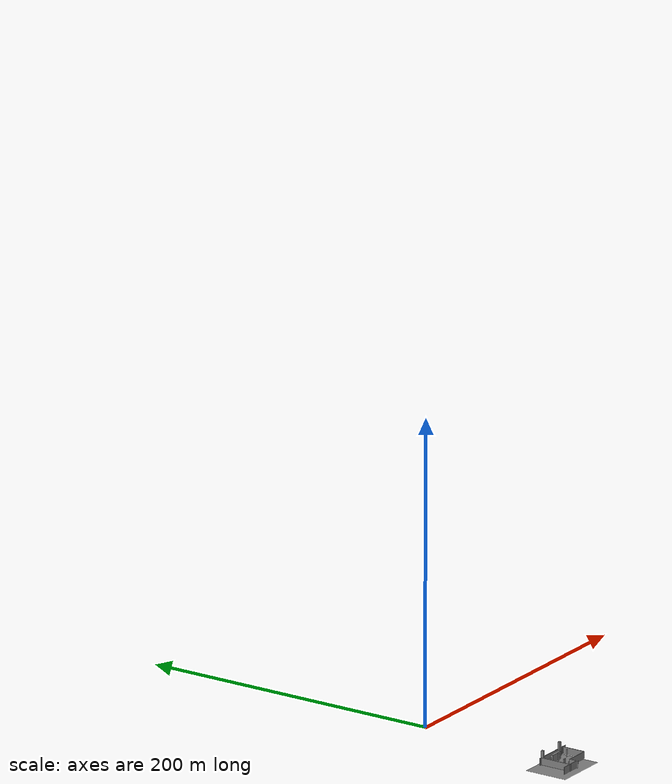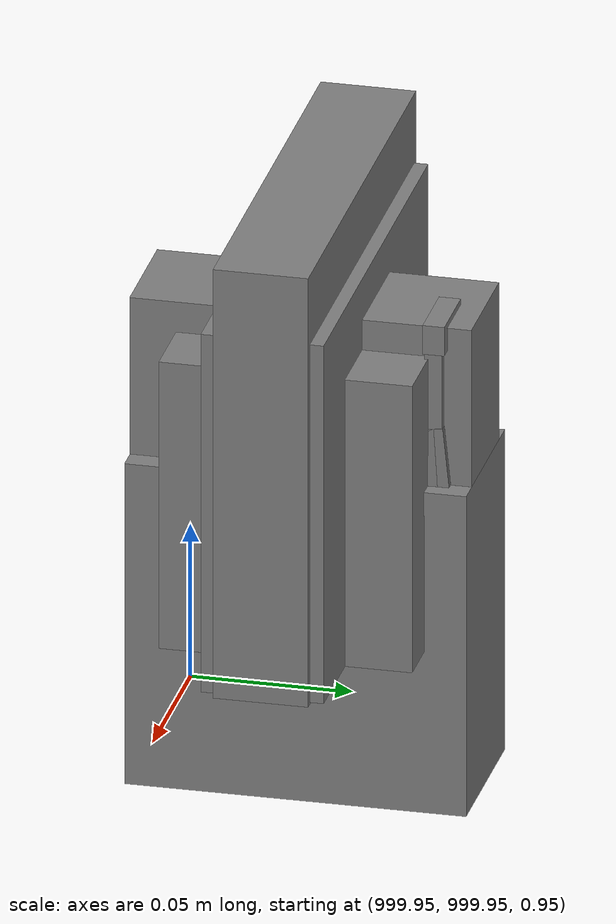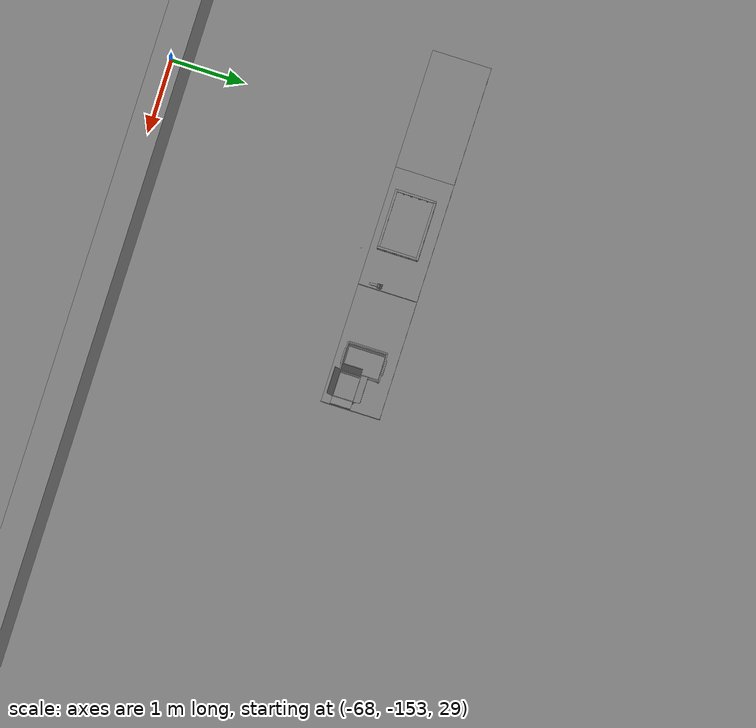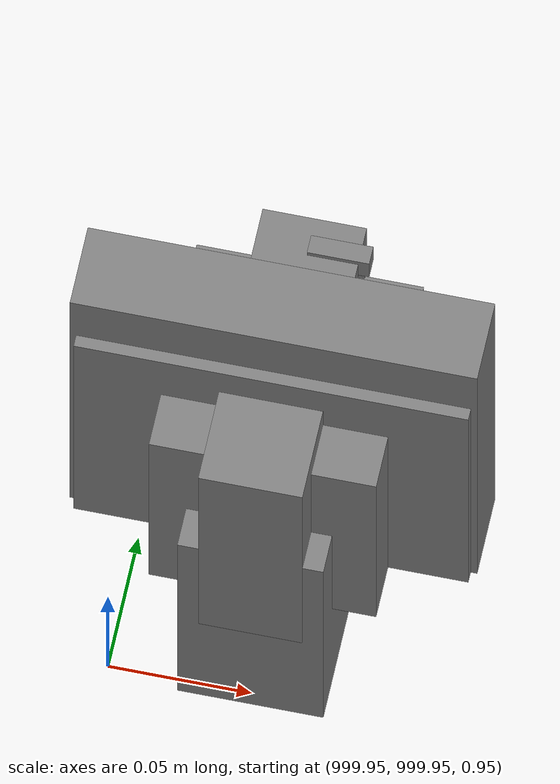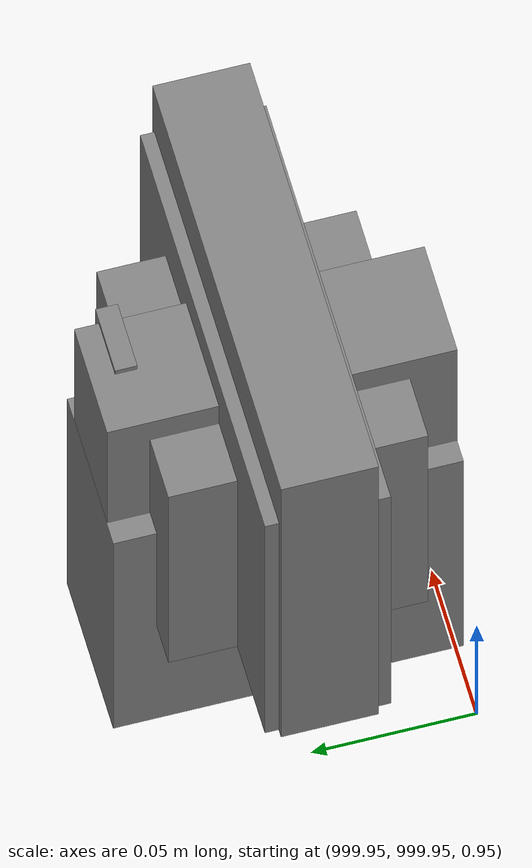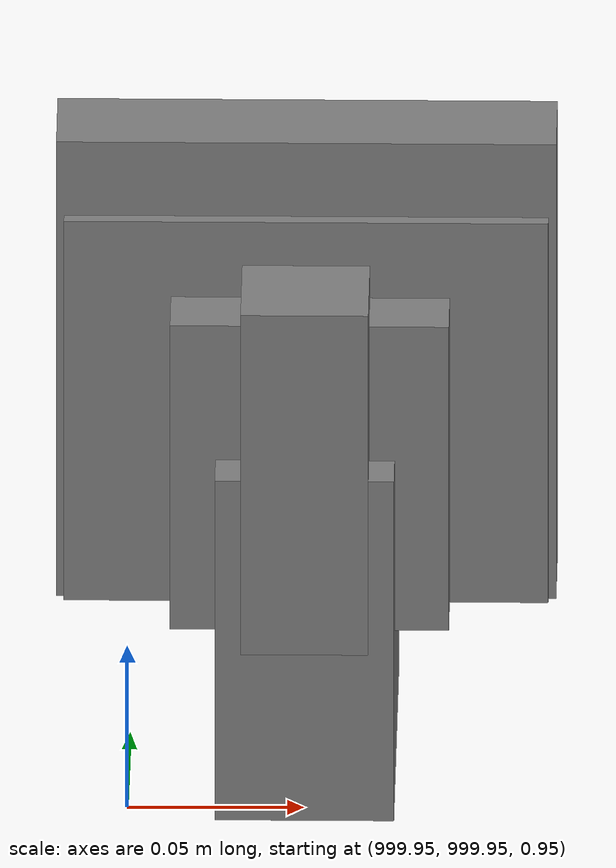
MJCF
<mujoco>
    <option gravity="0.000000000 0.000000000 -9.810000420" timestep="0.0049999999" integrator="implicitfast" density="1.225" viscosity="1.8000001e-05" noslip_iterations="10" iterations="100" sdf_iterations="50">
        <flag multiccd="disable"/>
    </option>
    <size memory="1000M"/>
    <compiler coordinate="local"/>
    <worldbody>
        <light cutoff="30" pos="0 1 1" dir="0 -1 -2"/>
        <light cutoff="30" pos="0 -1 1" dir="0 1 -2"/>
        <body pos="1000.000000000 1000.000000000 1.000000000" euler="0.000000000 0.000000000 180.000000000" name="openloong_gripper_2f85_fix_base_usda_cpu_fan">
            <geom contype="1" conaffinity="1" density="1000" type="box" material="" rgba="0.500000000 0.500000000 0.500000000 1.000000000" solimp="0.899999976 0.949999988 0.001000000" friction="1.000000000 0.005000000 0.000100000" solref="0.020000000 1.000000000" margin="0" condim="3" group="0" pos="0.000000000 0.000000000 0.070034981" quat="0.000000000 0.000000000 0.000000000 1.000000000" size="0.070700005 0.014699999 0.070700005" name="openloong_gripper_2f85_fix_base_usda_geom_85BBD2EC_46B0_4CF1_8254_657DDEDA47E2"/>
            <freejoint name="openloong_gripper_2f85_fix_base_usda_cpu_fan_joint"/>
            <site size="0.005000000 0.005000000 0.005000000" rgba="0.500000000 0.500000000 0.500000000 1.000000000" pos="0.000000000 0.000000000 0.000000000" quat="0.999961913 0.008726535 0.000000000 0.000000000" group="0" type="sphere" name="openloong_gripper_2f85_fix_base_usda_cpu_fancsite"/>
        </body>
        <body pos="1000.000000000 1000.000000000 1.000000000" euler="0.000011953 0.000005123 -179.999984741" name="openloong_gripper_2f85_fix_base_usda_intel_box">
            <geom contype="1" conaffinity="1" density="1000" type="box" material="" rgba="0.500000000 0.500000000 0.500000000 1.000000000" solimp="0.899999976 0.949999988 0.001000000" friction="1.000000000 0.005000000 0.000100000" solref="0.020000000 1.000000000" margin="0" condim="3" group="0" pos="0.000000000 -0.000067139 0.000082284" quat="0.707106709 0.000000225 0.000000253 0.707106650" size="0.052800003 0.025300000 0.052800003" name="openloong_gripper_2f85_fix_base_usda_geom_A7F194DF_7706_4714_A814_8F5D66E1E8BA"/>
            <freejoint name="openloong_gripper_2f85_fix_base_usda_intel_box_joint"/>
            <site size="0.005000000 0.005000000 0.005000000" rgba="0.500000000 0.500000000 0.500000000 1.000000000" pos="0.000000000 0.000000000 0.000000000" quat="0.999961913 0.008726500 0.000000000 0.000000000" group="0" type="sphere" name="openloong_gripper_2f85_fix_base_usda_intel_boxsite"/>
        </body>
        <body pos="1000.000000000 1000.000000000 1.000000000" euler="0.000000000 0.000000000 180.000000000" name="openloong_gripper_2f85_fix_base_usda_wifi_box">
            <geom contype="1" conaffinity="1" density="1000" type="box" material="" rgba="0.500000000 0.500000000 0.500000000 1.000000000" solimp="0.899999976 0.949999988 0.001000000" friction="1.000000000 0.005000000 0.000100000" solref="0.020000000 1.000000000" margin="0" condim="3" group="0" pos="0.000000000 0.000000000 0.058978677" quat="0.000000000 0.000000047 0.000000000 1.000000000" size="0.068499997 0.018999999 0.059000000" name="openloong_gripper_2f85_fix_base_usda_geom_ABEB577D_31DB_46D9_9C19_D4938FC3162C"/>
            <freejoint name="openloong_gripper_2f85_fix_base_usda_wifi_box_joint"/>
            <site size="0.005000000 0.005000000 0.005000000" rgba="0.500000000 0.500000000 0.500000000 1.000000000" pos="0.000000000 0.000000000 0.000000000" quat="0.999961913 0.008726500 0.000000000 0.000000000" group="0" type="sphere" name="openloong_gripper_2f85_fix_base_usda_wifi_boxsite"/>
        </body>
        <body pos="-66.291488647 -149.529663086 31.168136597" euler="170.162460327 73.793861389 151.401718140" mocap="true" name="spotlight4_SpotLight"/>
        <body pos="-66.101570129 -148.896347046 31.171756744" euler="-112.873641968 -51.493984222 132.726455688" mocap="true" name="spotlight1_SpotLight"/>
        <body pos="1000.000000000 1000.000000000 1.000000000" euler="0.000000000 0.000000000 180.000000000" name="openloong_gripper_2f85_fix_base_usda_battery_01">
            <geom contype="1" conaffinity="1" density="1000" type="box" material="" rgba="0.500000000 0.500000000 0.500000000 1.000000000" solimp="0.899999976 0.949999988 0.001000000" friction="1.000000000 0.005000000 0.000100000" solref="0.020000000 1.000000000" margin="0" condim="3" group="0" pos="-0.011123657 -0.041940309 0.101691343" quat="1.000000000 0.000000000 0.000000000 0.000000000" size="0.010800000 0.003375000 0.004725000" name="openloong_gripper_2f85_fix_base_usda_geom_119703C4_83E6_4424_9F58_753E0EA10BAF"/>
            <geom contype="1" conaffinity="1" density="1000" type="box" material="" rgba="0.500000000 0.500000000 0.500000000 1.000000000" solimp="0.899999976 0.949999988 0.001000000" friction="1.000000000 0.005000000 0.000100000" solref="0.020000000 1.000000000" margin="0" condim="3" group="0" pos="-0.010876465 -0.044247437 0.047066893" quat="0.998702705 -0.050920475 0.000000000 0.000000000" size="0.009450001 0.002700000 0.024975000" name="openloong_gripper_2f85_fix_base_usda_geom_6D5475B6_0FAC_48E2_95FB_1EC0FD35E8C5"/>
            <geom contype="1" conaffinity="1" density="1000" type="box" material="" rgba="0.500000000 0.500000000 0.500000000 1.000000000" solimp="0.899999976 0.949999988 0.001000000" friction="1.000000000 0.005000000 0.000100000" solref="0.020000000 1.000000000" margin="0" condim="3" group="0" pos="-0.001235962 -0.000659180 0.047381196" quat="1.000000000 0.000000000 0.000000000 0.000000000" size="0.039420001 0.039150000 0.047250003" name="openloong_gripper_2f85_fix_base_usda_geom_01F28BAF_8997_4F92_BF2C_2BA6C2C44DCF"/>
            <geom contype="1" conaffinity="1" density="1000" type="box" material="" rgba="0.500000000 0.500000000 0.500000000 1.000000000" solimp="0.899999976 0.949999988 0.001000000" friction="1.000000000 0.005000000 0.000100000" solref="0.020000000 1.000000000" margin="0" condim="3" group="0" pos="-0.010876465 -0.039138794 0.009851727" quat="1.000000000 0.000000000 0.000000000 0.000000000" size="0.009450001 0.010800000 0.013500000" name="openloong_gripper_2f85_fix_base_usda_geom_9B389980_1F98_4053_A92F_D54A5915F978"/>
            <geom contype="1" conaffinity="1" density="1000" type="box" material="" rgba="0.500000000 0.500000000 0.500000000 1.000000000" solimp="0.899999976 0.949999988 0.001000000" friction="1.000000000 0.005000000 0.000100000" solref="0.020000000 1.000000000" margin="0" condim="3" group="0" pos="-0.010876465 -0.041528322 0.071508206" quat="1.000000000 0.000000000 0.000000000 0.000000000" size="0.009450001 0.002700000 0.027000001" name="openloong_gripper_2f85_fix_base_usda_geom_DCD346BE_154F_4114_9717_0F02616CBE5B"/>
            <freejoint name="openloong_gripper_2f85_fix_base_usda_battery_01_joint"/>
            <site size="0.005000000 0.005000000 0.005000000" rgba="0.500000000 0.500000000 0.500000000 1.000000000" pos="0.000000000 0.000000000 0.000000000" quat="0.999961913 0.008726500 0.000000000 0.000000000" group="0" type="sphere" name="openloong_gripper_2f85_fix_base_usda_battery_01site"/>
        </body>
        <body pos="1000.000000000 999.999938965 1.000000000" euler="0.000000000 0.000000000 180.000000000" name="openloong_gripper_2f85_fix_base_usda_intelcore_i5">
            <geom contype="1" conaffinity="1" density="1000" type="box" material="" rgba="0.500000000 0.500000000 0.500000000 1.000000000" solimp="0.899999976 0.949999988 0.001000000" friction="1.000000000 0.005000000 0.000100000" solref="0.020000000 1.000000000" margin="0" condim="3" group="0" pos="0.000000000 0.000000000 0.051722717" quat="0.707106709 0.000000000 0.000000000 -0.707106769" size="0.052800000 0.018080002 0.052800000" name="openloong_gripper_2f85_fix_base_usda_geom_3D537CC1_9990_4F06_A647_FD9AE9C1FF94"/>
            <freejoint name="openloong_gripper_2f85_fix_base_usda_intelcore_i5_joint"/>
            <site size="0.005000000 0.005000000 0.005000000" rgba="0.500000000 0.500000000 0.500000000 1.000000000" pos="0.000000000 0.000000000 0.000000000" quat="0.999961913 0.008726534 0.000000000 0.000000000" group="0" type="sphere" name="openloong_gripper_2f85_fix_base_usda_intelcore_i5site"/>
        </body>
        <body pos="-66.367477417 -149.550643921 31.167776108" euler="69.326805115 -67.546073914 86.811973572" mocap="true" name="spotlight2_SpotLight"/>
        <body pos="-64.866622925 -149.383972168 30.183746338" euler="89.999984741 89.999946594 0.000000000" name="openloong_gripper_2f85_fix_base_usda_bluebox_01">
            <geom contype="1" conaffinity="1" density="1000" type="box" material="" rgba="0.500000000 0.500000000 0.500000000 1.000000000" solimp="0.899999976 0.949999988 0.001000000" friction="1.000000000 0.005000000 0.000100000" solref="0.020000000 1.000000000" margin="0" condim="3" group="0" pos="0.276580811 0.187225342 0.000068665" quat="0.707106948 0.000077471 0.707106352 0.000077486" size="0.100000001 0.057999998 0.010000000" name="openloong_gripper_2f85_fix_base_usda_geom_737DCBAC_6810_4AF9_B488_35B2F45C2B2C"/>
            <geom contype="1" conaffinity="1" density="1000" type="box" material="" rgba="0.500000000 0.500000000 0.500000000 1.000000000" solimp="0.899999976 0.949999988 0.001000000" friction="1.000000000 0.005000000 0.000100000" solref="0.020000000 1.000000000" margin="0" condim="3" group="0" pos="0.000000000 0.002883911 0.000000000" quat="0.999999881 0.000000000 0.000000000 0.000000000" size="0.254000008 0.003000000 0.172000006" name="openloong_gripper_2f85_fix_base_usda_geom_D513699C_00F1_45A2_A361_BDD625148470"/>
            <geom contype="1" conaffinity="1" density="1000" type="box" material="" rgba="0.500000000 0.500000000 0.500000000 1.000000000" solimp="0.899999976 0.949999988 0.001000000" friction="1.000000000 0.005000000 0.000100000" solref="0.020000000 1.000000000" margin="0" condim="3" group="0" pos="0.000000000 0.124874115 0.173484802" quat="0.999796331 0.020176515 -0.000000015 0.000000030" size="0.259999990 0.119999997 0.007000000" name="openloong_gripper_2f85_fix_base_usda_geom_12F464E5_AEF6_4C1B_BF3B_4D8FEFDDFA58"/>
            <geom contype="1" conaffinity="1" density="1000" type="box" material="" rgba="0.500000000 0.500000000 0.500000000 1.000000000" solimp="0.899999976 0.949999988 0.001000000" friction="1.000000000 0.005000000 0.000100000" solref="0.020000000 1.000000000" margin="0" condim="3" group="0" pos="0.000000000 0.124874115 -0.173469543" quat="0.999796331 -0.020176545 -0.000000015 0.000000000" size="0.259999990 0.119999997 0.007000000" name="openloong_gripper_2f85_fix_base_usda_geom_31B5E3B0_7A77_4452_A95C_B9540F10A7F8"/>
            <geom contype="1" conaffinity="1" density="1000" type="box" material="" rgba="0.500000000 0.500000000 0.500000000 1.000000000" solimp="0.899999976 0.949999988 0.001000000" friction="1.000000000 0.005000000 0.000100000" solref="0.020000000 1.000000000" margin="0" condim="3" group="0" pos="0.000000000 0.214008331 0.188980103" quat="0.999912977 0.013176724 0.000000015 0.000000000" size="0.259999990 0.029999999 0.012500000" name="openloong_gripper_2f85_fix_base_usda_geom_10110E61_36F5_4B2E_A07E_80A82C7F66F0"/>
            <geom contype="1" conaffinity="1" density="1000" type="box" material="" rgba="0.500000000 0.500000000 0.500000000 1.000000000" solimp="0.899999976 0.949999988 0.001000000" friction="1.000000000 0.005000000 0.000100000" solref="0.020000000 1.000000000" margin="0" condim="3" group="0" pos="-0.258361816 0.125289917 0.001876831" quat="0.702796936 -0.020792112 0.710783124 0.020769298" size="0.189999998 0.119999997 0.009000000" name="openloong_gripper_2f85_fix_base_usda_geom_8252856B_6846_4D44_BFF3_8357CEBE5D88"/>
            <geom contype="1" conaffinity="1" density="1000" type="box" material="" rgba="0.500000000 0.500000000 0.500000000 1.000000000" solimp="0.899999976 0.949999988 0.001000000" friction="1.000000000 0.005000000 0.000100000" solref="0.020000000 1.000000000" margin="0" condim="3" group="0" pos="0.000000000 0.214008331 -0.188980103" quat="0.999912977 -0.013176769 0.000000030 0.000000015" size="0.259999990 0.029999999 0.012500000" name="openloong_gripper_2f85_fix_base_usda_geom_EDCC8FAE_8498_4F2F_8253_AC3AB467DB7B"/>
            <geom contype="1" conaffinity="1" density="1000" type="box" material="" rgba="0.500000000 0.500000000 0.500000000 1.000000000" solimp="0.899999976 0.949999988 0.001000000" friction="1.000000000 0.005000000 0.000100000" solref="0.020000000 1.000000000" margin="0" condim="3" group="0" pos="-0.276611328 0.187225342 0.000068665" quat="0.707106650 0.000077441 0.707106709 0.000077456" size="0.100000001 0.057999998 0.010000000" name="openloong_gripper_2f85_fix_base_usda_geom_E27B0FDC_9D4D_4715_BB6F_9E63844CD09A"/>
            <geom contype="1" conaffinity="1" density="1000" type="box" material="" rgba="0.500000000 0.500000000 0.500000000 1.000000000" solimp="0.899999976 0.949999988 0.001000000" friction="1.000000000 0.005000000 0.000100000" solref="0.020000000 1.000000000" margin="0" condim="3" group="0" pos="0.258331299 0.125289917 0.001876831" quat="0.702851415 0.018856421 0.710823774 -0.019329369" size="0.189999998 0.119999997 0.009000000" name="openloong_gripper_2f85_fix_base_usda_geom_13C9E70B_43DF_419B_9C22_8977BAE72131"/>
            <freejoint name="openloong_gripper_2f85_fix_base_usda_bluebox_01_joint"/>
            <site size="0.005000000 0.005000000 0.005000000" rgba="0.500000000 0.500000000 0.500000000 1.000000000" pos="0.000000000 0.000000000 0.000000000" quat="0.999961913 0.008726534 0.000000000 0.000000000" group="0" type="sphere" name="openloong_gripper_2f85_fix_base_usda_bluebox_01site"/>
        </body>
        <body pos="-64.496299744 -149.491867065 30.235729218" euler="0.000000000 0.000000000 89.999946594" name="openloong_gripper_2f85_fix_base_usda_cardboardbox_01">
            <geom contype="1" conaffinity="1" density="1000" type="box" material="" rgba="0.500000000 0.500000000 0.500000000 1.000000000" solimp="0.899999976 0.949999988 0.001000000" friction="1.000000000 0.005000000 0.000100000" solref="0.020000000 1.000000000" margin="0" condim="3" group="0" pos="-0.003166199 -0.004086494 0.005052090" quat="1.000000000 0.000000000 0.000000000 0.000000000" size="0.142499998 0.177500010 0.005000000" name="openloong_gripper_2f85_fix_base_usda_geom_9C55C4F1_D8B9_4990_A195_219B9E569BD2"/>
            <geom contype="1" conaffinity="1" density="1000" type="box" material="" rgba="0.500000000 0.500000000 0.500000000 1.000000000" solimp="0.899999976 0.949999988 0.001000000" friction="1.000000000 0.005000000 0.000100000" solref="0.020000000 1.000000000" margin="0" condim="3" group="0" pos="-0.003166199 0.170316696 0.150570869" quat="1.000000000 0.000000000 0.000000000 0.000000000" size="0.142499998 0.005000000 0.149999991" name="openloong_gripper_2f85_fix_base_usda_geom_4D9B46C1_FD2E_4953_B823_AC9100F1ADF0"/>
            <geom contype="1" conaffinity="1" density="1000" type="box" material="" rgba="0.500000000 0.500000000 0.500000000 1.000000000" solimp="0.899999976 0.949999988 0.001000000" friction="1.000000000 0.005000000 0.000100000" solref="0.020000000 1.000000000" margin="0" condim="3" group="0" pos="-0.147399902 -0.005307198 0.150570869" quat="1.000000000 0.000000000 0.000000000 0.000000000" size="0.005000000 0.177500010 0.149999991" name="openloong_gripper_2f85_fix_base_usda_geom_701315D7_EAB2_47F5_9F45_B16BEE670F7A"/>
            <geom contype="1" conaffinity="1" density="1000" type="box" material="" rgba="0.500000000 0.500000000 0.500000000 1.000000000" solimp="0.899999976 0.949999988 0.001000000" friction="1.000000000 0.005000000 0.000100000" solref="0.020000000 1.000000000" margin="0" condim="3" group="0" pos="0.140275955 -0.005307198 0.150570869" quat="1.000000000 0.000000000 0.000000000 0.000000000" size="0.005000000 0.177500010 0.149999991" name="openloong_gripper_2f85_fix_base_usda_geom_BBA60732_B4C3_4A56_A55D_5A4E50640B63"/>
            <geom contype="1" conaffinity="1" density="1000" type="box" material="" rgba="0.500000000 0.500000000 0.500000000 1.000000000" solimp="0.899999976 0.949999988 0.001000000" friction="1.000000000 0.005000000 0.000100000" solref="0.020000000 1.000000000" margin="0" condim="3" group="0" pos="-0.003166199 -0.181550980 0.150570869" quat="1.000000000 0.000000000 0.000000000 0.000000000" size="0.142499998 0.005000000 0.149999991" name="openloong_gripper_2f85_fix_base_usda_geom_7C00A9DB_2E7C_40FA_9A96_35720F993EEC"/>
            <freejoint name="openloong_gripper_2f85_fix_base_usda_cardboardbox_01_joint"/>
            <site size="0.005000000 0.005000000 0.005000000" rgba="0.500000000 0.500000000 0.500000000 1.000000000" pos="0.000000000 0.000000000 0.000000000" quat="0.999961913 0.008726535 0.000000000 0.000000000" group="0" type="sphere" name="openloong_gripper_2f85_fix_base_usda_site_8A41AC00_4BF2_4F2D_B0C9_2D1BE22F63AE"/>
            <body pos="0.139160156 -0.004048347 0.301930904" euler="-179.999954224 49.383502960 179.999954224" name="openloong_gripper_2f85_fix_base_usda_A1_006">
                <geom contype="1" conaffinity="1" density="1000" type="box" material="" rgba="0.500000000 0.500000000 0.500000000 1.000000000" solimp="0.899999976 0.949999988 0.001000000" friction="1.000000000 0.005000000 0.000100000" solref="0.020000000 1.000000000" margin="0" condim="3" group="0" pos="-0.071587563 0.000009537 0.001745224" quat="0.999999881 0.000000000 0.000000000 0.000000000" size="0.071249999 0.179999992 0.002500000" name="openloong_gripper_2f85_fix_base_usda_geom_084BD9EB_C2DE_4346_9F93_1B714E71892D"/>
                <joint armature="0" stiffness="0.07" damping="0.0099999998" axis="0.000000 1.000000 0.000000" type="hinge" name="openloong_gripper_2f85_fix_base_usda_A1_006"/>
            </body>
            <body pos="-0.145902634 -0.004086494 0.301938057" euler="-180.000000000 -60.000011444 -180.000000000" name="openloong_gripper_2f85_fix_base_usda_A2_006">
                <geom contype="1" conaffinity="1" density="1000" type="box" material="" rgba="0.500000000 0.500000000 0.500000000 1.000000000" solimp="0.899999976 0.949999988 0.001000000" friction="1.000000000 0.005000000 0.000100000" solref="0.020000000 1.000000000" margin="0" condim="3" group="0" pos="0.071268082 0.000009537 0.002717972" quat="0.000002921 0.000000000 -0.000000030 0.999999881" size="0.071249999 0.179999992 0.002500000" name="openloong_gripper_2f85_fix_base_usda_geom_C4C1BA78_E08E_479E_9232_45670B4FD43E"/>
                <joint armature="0" stiffness="0.07" damping="0.0099999998" axis="0.000000 1.000000 0.000000" type="hinge" name="openloong_gripper_2f85_fix_base_usda_A2_006"/>
            </body>
            <body pos="-0.003385544 0.175991058 0.301930904" euler="-125.858116150 -0.000004561 0.000002331" name="openloong_gripper_2f85_fix_base_usda_B2_006">
                <geom contype="1" conaffinity="1" density="1000" type="box" material="" rgba="0.500000000 0.500000000 0.500000000 1.000000000" solimp="0.899999976 0.949999988 0.001000000" friction="1.000000000 0.005000000 0.000100000" solref="0.020000000 1.000000000" margin="0" condim="3" group="0" pos="0.000009537 -0.070939064 -0.002470016" quat="0.999614120 0.027776197 -0.000000015 0.000000030" size="0.137500003 0.064999998 0.005000000" name="openloong_gripper_2f85_fix_base_usda_geom_8EDB8786_F908_4CAA_BCAE_F7F177E49B16"/>
                <joint armature="0" stiffness="0.07" damping="0.0099999998" axis="1.000000 0.000000 0.000000" type="hinge" name="openloong_gripper_2f85_fix_base_usda_B2_006"/>
            </body>
            <body pos="-0.003385544 -0.184140205 0.301938057" euler="147.805557251 0.000000000 0.000000000" name="openloong_gripper_2f85_fix_base_usda_B1_006">
                <geom contype="1" conaffinity="1" density="1000" type="box" material="" rgba="0.500000000 0.500000000 0.500000000 1.000000000" solimp="0.899999976 0.949999988 0.001000000" friction="1.000000000 0.005000000 0.000100000" solref="0.020000000 1.000000000" margin="0" condim="3" group="0" pos="-0.000028610 0.070202351 -0.002703667" quat="0.999614179 -0.027776167 0.000000000 0.000000000" size="0.137500003 0.064999998 0.005000000" name="openloong_gripper_2f85_fix_base_usda_geom_BD105B3F_12AC_4DC7_997C_952C60DDE571"/>
                <joint armature="0" stiffness="0.07" damping="0.0099999998" axis="1.000000 0.000000 0.000000" type="hinge" name="openloong_gripper_2f85_fix_base_usda_B1_006"/>
            </body>
        </body>
        <body pos="-65.882858276 -149.481979370 30.229999542" euler="-64.487716675 0.000000000 0.000000000" name="openloong_gripper_2f85_fix_base_usda_Barcode">
            <geom contype="1" conaffinity="1" density="1000" type="box" material="" rgba="0.500000000 0.500000000 0.500000000 1.000000000" solimp="0.899999976 0.949999988 0.001000000" friction="1.000000000 0.005000000 0.000100000" solref="0.020000000 1.000000000" margin="0" condim="3" group="0" pos="0.000000000 0.013038635 0.001419067" quat="0.000000000 0.000000000 0.000000000 1.000000119" size="0.034000002 0.010000000 0.017999999" name="openloong_gripper_2f85_fix_base_usda_geom_4586F672_C3F9_4988_B9A3_FAE388D5932E"/>
            <geom contype="1" conaffinity="1" density="1000" type="box" material="" rgba="0.500000000 0.500000000 0.500000000 1.000000000" solimp="0.899999976 0.949999988 0.001000000" friction="1.000000000 0.005000000 0.000100000" solref="0.020000000 1.000000000" margin="0" condim="3" group="0" pos="0.000000000 -0.035301208 -0.007095337" quat="0.000000000 0.000000000 -0.043619365 0.999048233" size="0.028999999 0.010000000 0.020000000" name="openloong_gripper_2f85_fix_base_usda_geom_09190574_5E6F_4765_B96E_E91CE4D8B38F"/>
            <geom contype="1" conaffinity="1" density="1000" type="box" material="" rgba="0.500000000 0.500000000 0.500000000 1.000000000" solimp="0.899999976 0.949999988 0.001000000" friction="1.000000000 0.005000000 0.000100000" solref="0.020000000 1.000000000" margin="0" condim="3" group="0" pos="0.000000000 -0.043411255 -0.011749268" quat="0.922262907 0.386563420 0.000000000 0.000000000" size="0.026000001 0.010000000 0.020000000" name="openloong_gripper_2f85_fix_base_usda_geom_E1B38D9F_D44F_4B42_B8C3_1E1CEC503B34"/>
            <geom contype="1" conaffinity="1" density="1000" type="box" material="" rgba="0.500000000 0.500000000 0.500000000 1.000000000" solimp="0.899999976 0.949999988 0.001000000" friction="1.000000000 0.005000000 0.000100000" solref="0.020000000 1.000000000" margin="0" condim="3" group="0" pos="0.000000000 -0.016967773 -0.031860352" quat="0.000000000 0.000000000 0.000000000 1.000000119" size="0.008000000 0.010000000 0.013000000" name="openloong_gripper_2f85_fix_base_usda_geom_8A520687_4B12_4FFE_986B_E143717F6E4E"/>
            <geom contype="1" conaffinity="1" density="1000" type="box" material="" rgba="0.500000000 0.500000000 0.500000000 1.000000000" solimp="0.899999976 0.949999988 0.001000000" friction="1.000000000 0.005000000 0.000100000" solref="0.020000000 1.000000000" margin="0" condim="3" group="0" pos="0.000000000 -0.001869202 0.000312805" quat="0.953716993 0.300705761 0.000000000 0.000000000" size="0.032000002 0.010000000 0.018999999" name="openloong_gripper_2f85_fix_base_usda_geom_7DACA0BA_1C48_426D_8CDA_4AE0216DE7FE"/>
            <geom contype="1" conaffinity="1" density="1000" type="box" material="" rgba="0.500000000 0.500000000 0.500000000 1.000000000" solimp="0.899999976 0.949999988 0.001000000" friction="1.000000000 0.005000000 0.000100000" solref="0.020000000 1.000000000" margin="0" condim="3" group="0" pos="0.000000000 -0.019531250 -0.003173828" quat="0.953716993 0.300705761 0.000000000 0.000000000" size="0.030999999 0.010000000 0.020000000" name="openloong_gripper_2f85_fix_base_usda_geom_3FF34835_3C35_4928_BE77_82B37ACE93AA"/>
            <geom contype="1" conaffinity="1" density="1000" type="box" material="" rgba="0.500000000 0.500000000 0.500000000 1.000000000" solimp="0.899999976 0.949999988 0.001000000" friction="1.000000000 0.005000000 0.000100000" solref="0.020000000 1.000000000" margin="0" condim="3" group="0" pos="0.000000000 -0.035301208 -0.007095337" quat="0.953716993 0.300705761 0.000000000 0.000000000" size="0.028999999 0.010000000 0.020000000" name="openloong_gripper_2f85_fix_base_usda_geom_D24CA65E_1C75_43C8_8D17_77FC174F939C"/>
            <geom contype="1" conaffinity="1" density="1000" type="box" material="" rgba="0.500000000 0.500000000 0.500000000 1.000000000" solimp="0.899999976 0.949999988 0.001000000" friction="1.000000000 0.005000000 0.000100000" solref="0.020000000 1.000000000" margin="0" condim="3" group="0" pos="0.000000000 -0.042617798 -0.071121216" quat="0.000000000 0.000000000 0.000000000 1.000000119" size="0.013000000 0.021000000 0.059999999" name="openloong_gripper_2f85_fix_base_usda_geom_422C7E4A_4495_43F2_9F5A_967B961836D6"/>
            <freejoint name="openloong_gripper_2f85_fix_base_usda_Barcode_joint"/>
            <site size="0.005000000 0.005000000 0.005000000" rgba="0.500000000 0.500000000 0.500000000 1.000000000" pos="0.000000000 0.000000000 0.000000000" quat="1.000000000 0.000000000 0.000000000 0.000000000" group="0" type="sphere" name="openloong_gripper_2f85_fix_base_usda_Barcode_site"/>
        </body>
        <body pos="-66.745018005 -149.392349243 30.184000015" euler="0.000000000 0.000000000 89.999946594" name="[22329756425338]_Basket_01">
            <geom contype="1" conaffinity="1" density="1000" type="box" material="" rgba="0.500000000 0.500000000 0.500000000 1.000000000" solimp="0.899999976 0.949999988 0.001000000" friction="1.000000000 0.005000000 0.000100000" solref="0.020000000 1.000000000" margin="0" condim="3" group="0" pos="-0.052425385 0.389207840 0.089787483" quat="0.707107008 0.000000000 0.000000000 0.707106411" size="0.014249999 0.014249999 0.059999999" name="[22329756425338]_geom_F0806434_69FA_42DB_B910_83E9DD2FCA6E"/>
            <geom contype="1" conaffinity="1" density="1000" type="box" material="" rgba="0.500000000 0.500000000 0.500000000 1.000000000" solimp="0.899999976 0.949999988 0.001000000" friction="1.000000000 0.005000000 0.000100000" solref="0.020000000 1.000000000" margin="0" condim="3" group="0" pos="0.264015198 -0.133043289 0.089787483" quat="0.707107008 0.000000000 0.000000000 0.707106411" size="0.014249999 0.014249999 0.059999999" name="[22329756425338]_geom_A4884932_E2EF_4A02_B3A9_1E826B115DC2"/>
            <geom contype="1" conaffinity="1" density="1000" type="box" material="" rgba="0.500000000 0.500000000 0.500000000 1.000000000" solimp="0.899999976 0.949999988 0.001000000" friction="1.000000000 0.005000000 0.000100000" solref="0.020000000 1.000000000" margin="0" condim="3" group="0" pos="-0.264015198 -0.265548706 0.089793205" quat="0.707107008 0.000000000 0.000000000 0.707106411" size="0.014249999 0.014249999 0.059999999" name="[22329756425338]_geom_FC9F9200_43F2_48C6_A589_2894BBFC363C"/>
            <geom contype="1" conaffinity="1" density="1000" type="box" material="" rgba="0.500000000 0.500000000 0.500000000 1.000000000" solimp="0.899999976 0.949999988 0.001000000" friction="1.000000000 0.005000000 0.000100000" solref="0.020000000 1.000000000" margin="0" condim="3" group="0" pos="-0.160263062 -0.389322281 0.089793205" quat="0.707107008 0.000000000 0.000000000 0.707106411" size="0.014249999 0.014249999 0.059999999" name="[22329756425338]_geom_1CC84D24_BAA1_44EF_81B3_121434FFD9AD"/>
            <geom contype="1" conaffinity="1" density="1000" type="box" material="" rgba="0.500000000 0.500000000 0.500000000 1.000000000" solimp="0.899999976 0.949999988 0.001000000" friction="1.000000000 0.005000000 0.000100000" solref="0.020000000 1.000000000" margin="0" condim="3" group="0" pos="0.162265778 -0.389322281 0.089787483" quat="0.707107008 0.000000000 0.000000000 0.707106411" size="0.014249999 0.014249999 0.059999999" name="[22329756425338]_geom_9FC81E07_27A3_41DF_95F7_FE79E8CDEA2D"/>
            <geom contype="1" conaffinity="1" density="1000" type="box" material="" rgba="0.500000000 0.500000000 0.500000000 1.000000000" solimp="0.899999976 0.949999988 0.001000000" friction="1.000000000 0.005000000 0.000100000" solref="0.020000000 1.000000000" margin="0" condim="3" group="0" pos="0.264015198 0.389207840 0.089787483" quat="0.707107008 0.000000000 0.000000000 0.707106411" size="0.014249999 0.014249999 0.059999999" name="[22329756425338]_geom_45E82135_1EBA_4B98_B44F_472179C6A6AF"/>
            <geom contype="1" conaffinity="1" density="1000" type="box" material="" rgba="0.500000000 0.500000000 0.500000000 1.000000000" solimp="0.899999976 0.949999988 0.001000000" friction="1.000000000 0.005000000 0.000100000" solref="0.020000000 1.000000000" margin="0" condim="3" group="0" pos="-0.264015198 -0.133043289 0.089793205" quat="0.707107008 0.000000000 0.000000000 0.707106411" size="0.014249999 0.014249999 0.059999999" name="[22329756425338]_geom_A44BD7D7_BDA3_4E78_896F_E842762F62DF"/>
            <geom contype="1" conaffinity="1" density="1000" type="box" material="" rgba="0.500000000 0.500000000 0.500000000 1.000000000" solimp="0.899999976 0.949999988 0.001000000" friction="1.000000000 0.005000000 0.000100000" solref="0.020000000 1.000000000" margin="0" condim="3" group="0" pos="-0.264026642 0.269256592 0.089793205" quat="0.707107008 0.000000000 0.000000000 0.707106411" size="0.014249999 0.014249999 0.059999999" name="[22329756425338]_geom_718CA7E0_F0DD_4F35_A030_7D0489D807E9"/>
            <geom contype="1" conaffinity="1" density="1000" type="box" material="" rgba="0.500000000 0.500000000 0.500000000 1.000000000" solimp="0.899999976 0.949999988 0.001000000" friction="1.000000000 0.005000000 0.000100000" solref="0.020000000 1.000000000" margin="0" condim="3" group="0" pos="0.054462433 0.389207840 0.089787483" quat="0.707107008 0.000000000 0.000000000 0.707106411" size="0.014249999 0.014249999 0.059999999" name="[22329756425338]_geom_FC9ACD46_3BB8_487E_AF67_425519187E52"/>
            <geom contype="1" conaffinity="1" density="1000" type="box" material="" rgba="0.500000000 0.500000000 0.500000000 1.000000000" solimp="0.899999976 0.949999988 0.001000000" friction="1.000000000 0.005000000 0.000100000" solref="0.020000000 1.000000000" margin="0" condim="3" group="0" pos="0.054462433 -0.389322281 0.089787483" quat="0.707107008 0.000000000 0.000000000 0.707106411" size="0.014249999 0.014249999 0.059999999" name="[22329756425338]_geom_F8992281_73FA_4920_95EC_61906A1F6A38"/>
            <geom contype="1" conaffinity="1" density="1000" type="box" material="" rgba="0.500000000 0.500000000 0.500000000 1.000000000" solimp="0.899999976 0.949999988 0.001000000" friction="1.000000000 0.005000000 0.000100000" solref="0.020000000 1.000000000" margin="0" condim="3" group="0" pos="0.264015198 0.269256592 0.089793205" quat="0.707107008 0.000000000 0.000000000 0.707106411" size="0.014249999 0.014249999 0.059999999" name="[22329756425338]_geom_CBC4ACBE_4E43_4D39_8684_CA9B1A2E7A43"/>
            <geom contype="1" conaffinity="1" density="1000" type="box" material="" rgba="0.500000000 0.500000000 0.500000000 1.000000000" solimp="0.899999976 0.949999988 0.001000000" friction="1.000000000 0.005000000 0.000100000" solref="0.020000000 1.000000000" margin="0" condim="3" group="0" pos="0.264015198 -0.389322281 0.089787483" quat="0.707107008 0.000000000 0.000000000 0.707106411" size="0.014249999 0.014249999 0.059999999" name="[22329756425338]_geom_9A363941_FB70_4FA5_BF21_BB53E7E43ED0"/>
            <geom contype="1" conaffinity="1" density="1000" type="box" material="" rgba="0.500000000 0.500000000 0.500000000 1.000000000" solimp="0.899999976 0.949999988 0.001000000" friction="1.000000000 0.005000000 0.000100000" solref="0.020000000 1.000000000" margin="0" condim="3" group="0" pos="0.000000000 0.000000000 0.015998840" quat="0.707107008 0.000000000 0.000000000 0.707106411" size="0.403499991 0.279000014 0.015750000" name="[22329756425338]_geom_DD682876_54E1_46DA_AFAB_BEDDDDA4973F"/>
            <geom contype="1" conaffinity="1" density="1000" type="box" material="" rgba="0.500000000 0.500000000 0.500000000 1.000000000" solimp="0.899999976 0.949999988 0.001000000" friction="1.000000000 0.005000000 0.000100000" solref="0.020000000 1.000000000" margin="0" condim="3" group="0" pos="0.000000000 -0.389476776 0.163619041" quat="0.707107008 0.000000000 0.000000000 0.707106411" size="0.015000000 0.277500004 0.015750000" name="[22329756425338]_geom_68ED1A50_B802_4C23_9C46_49B3E5384295"/>
            <geom contype="1" conaffinity="1" density="1000" type="box" material="" rgba="0.500000000 0.500000000 0.500000000 1.000000000" solimp="0.899999976 0.949999988 0.001000000" friction="1.000000000 0.005000000 0.000100000" solref="0.020000000 1.000000000" margin="0" condim="3" group="0" pos="0.162265778 0.389207840 0.089787483" quat="0.707107008 0.000000000 0.000000000 0.707106411" size="0.014249999 0.014249999 0.059999999" name="[22329756425338]_geom_E794589A_2ABD_4982_8EB7_44D598E506FC"/>
            <geom contype="1" conaffinity="1" density="1000" type="box" material="" rgba="0.500000000 0.500000000 0.500000000 1.000000000" solimp="0.899999976 0.949999988 0.001000000" friction="1.000000000 0.005000000 0.000100000" solref="0.020000000 1.000000000" margin="0" condim="3" group="0" pos="0.000000000 0.389471054 0.163619041" quat="0.707107008 0.000000000 0.000000000 0.707106411" size="0.015000000 0.277500004 0.015750000" name="[22329756425338]_geom_43ED167B_4321_49DC_94E5_2A01DA63E658"/>
            <geom contype="1" conaffinity="1" density="1000" type="box" material="" rgba="0.500000000 0.500000000 0.500000000 1.000000000" solimp="0.899999976 0.949999988 0.001000000" friction="1.000000000 0.005000000 0.000100000" solref="0.020000000 1.000000000" margin="0" condim="3" group="0" pos="-0.263511658 0.000000000 0.163619041" quat="0.707107008 0.000000000 0.000000000 0.707106411" size="0.403499991 0.015000000 0.015750000" name="[22329756425338]_geom_145C7485_5C25_4E33_9419_4404F5926B32"/>
            <geom contype="1" conaffinity="1" density="1000" type="box" material="" rgba="0.500000000 0.500000000 0.500000000 1.000000000" solimp="0.899999976 0.949999988 0.001000000" friction="1.000000000 0.005000000 0.000100000" solref="0.020000000 1.000000000" margin="0" condim="3" group="0" pos="-0.264015198 0.141334534 0.089793205" quat="0.707107008 0.000000000 0.000000000 0.707106411" size="0.014249999 0.014249999 0.059999999" name="[22329756425338]_geom_450D4003_866E_4192_875E_85D46BFE32A3"/>
            <geom contype="1" conaffinity="1" density="1000" type="box" material="" rgba="0.500000000 0.500000000 0.500000000 1.000000000" solimp="0.899999976 0.949999988 0.001000000" friction="1.000000000 0.005000000 0.000100000" solref="0.020000000 1.000000000" margin="0" condim="3" group="0" pos="0.264015198 -0.265548706 0.089787483" quat="0.707107008 0.000000000 0.000000000 0.707106411" size="0.014249999 0.014249999 0.059999999" name="[22329756425338]_geom_07A71458_A727_4D58_83B6_4F850796CF72"/>
            <geom contype="1" conaffinity="1" density="1000" type="box" material="" rgba="0.500000000 0.500000000 0.500000000 1.000000000" solimp="0.899999976 0.949999988 0.001000000" friction="1.000000000 0.005000000 0.000100000" solref="0.020000000 1.000000000" margin="0" condim="3" group="0" pos="-0.160263062 0.389207840 0.089787483" quat="0.707107008 0.000000000 0.000000000 0.707106411" size="0.014249999 0.014249999 0.059999999" name="[22329756425338]_geom_CA7D9E43_D184_42BC_B2BC_9AF62A315152"/>
            <geom contype="1" conaffinity="1" density="1000" type="box" material="" rgba="0.500000000 0.500000000 0.500000000 1.000000000" solimp="0.899999976 0.949999988 0.001000000" friction="1.000000000 0.005000000 0.000100000" solref="0.020000000 1.000000000" margin="0" condim="3" group="0" pos="-0.052425385 -0.389322281 0.089787483" quat="0.707107008 0.000000000 0.000000000 0.707106411" size="0.014249999 0.014249999 0.059999999" name="[22329756425338]_geom_36642C8D_CBF4_4696_AAF9_5306DD9C9E5A"/>
            <geom contype="1" conaffinity="1" density="1000" type="box" material="" rgba="0.500000000 0.500000000 0.500000000 1.000000000" solimp="0.899999976 0.949999988 0.001000000" friction="1.000000000 0.005000000 0.000100000" solref="0.020000000 1.000000000" margin="0" condim="3" group="0" pos="-0.264026642 -0.389322281 0.089793205" quat="0.707107008 0.000000000 0.000000000 0.707106411" size="0.014249999 0.014249999 0.059999999" name="[22329756425338]_geom_4FC358E1_754D_4C08_97CC_15D2574CCFAC"/>
            <geom contype="1" conaffinity="1" density="1000" type="box" material="" rgba="0.500000000 0.500000000 0.500000000 1.000000000" solimp="0.899999976 0.949999988 0.001000000" friction="1.000000000 0.005000000 0.000100000" solref="0.020000000 1.000000000" margin="0" condim="3" group="0" pos="0.264015198 0.141334534 0.089787483" quat="0.707107008 0.000000000 0.000000000 0.707106411" size="0.014249999 0.014249999 0.059999999" name="[22329756425338]_geom_10CA06A2_C665_4D1C_8E8B_4D84637CF53B"/>
            <geom contype="1" conaffinity="1" density="1000" type="box" material="" rgba="0.500000000 0.500000000 0.500000000 1.000000000" solimp="0.899999976 0.949999988 0.001000000" friction="1.000000000 0.005000000 0.000100000" solref="0.020000000 1.000000000" margin="0" condim="3" group="0" pos="-0.264015198 0.389207840 0.089793205" quat="0.707107008 0.000000000 0.000000000 0.707106411" size="0.014249999 0.014249999 0.059999999" name="[22329756425338]_geom_38407A71_7736_4138_B258_924F52B523AE"/>
            <geom contype="1" conaffinity="1" density="1000" type="box" material="" rgba="0.500000000 0.500000000 0.500000000 1.000000000" solimp="0.899999976 0.949999988 0.001000000" friction="1.000000000 0.005000000 0.000100000" solref="0.020000000 1.000000000" margin="0" condim="3" group="0" pos="0.264015198 0.004480362 0.089787483" quat="0.707107008 0.000000000 0.000000000 0.707106411" size="0.014249999 0.014249999 0.059999999" name="[22329756425338]_geom_7BA6B06B_D5C1_4443_8E7C_338963D0D938"/>
            <geom contype="1" conaffinity="1" density="1000" type="box" material="" rgba="0.500000000 0.500000000 0.500000000 1.000000000" solimp="0.899999976 0.949999988 0.001000000" friction="1.000000000 0.005000000 0.000100000" solref="0.020000000 1.000000000" margin="0" condim="3" group="0" pos="0.263694763 -0.000011444 0.163619041" quat="0.707107008 0.000000000 0.000000000 0.707106411" size="0.403499991 0.015000000 0.015750000" name="[22329756425338]_geom_8F94BEBE_4685_4667_A084_70733AAAF96A"/>
            <geom contype="1" conaffinity="1" density="1000" type="box" material="" rgba="0.500000000 0.500000000 0.500000000 1.000000000" solimp="0.899999976 0.949999988 0.001000000" friction="1.000000000 0.005000000 0.000100000" solref="0.020000000 1.000000000" margin="0" condim="3" group="0" pos="-0.264015198 0.004480362 0.089793205" quat="0.707107008 0.000000000 0.000000000 0.707106411" size="0.014249999 0.014249999 0.059999999" name="[22329756425338]_geom_3CFFBA0B_C52E_4BF2_AB2C_F1B3D441FFD2"/>
            <freejoint name="[22329756425338]_joint_A2EE9680_C1DA_4C8C_B741_E4F1443B4AF5"/>
        </body>
        <body pos="0.000000000 0.000000000 0.000000000" euler="0.000000000 0.000000000 0.000000000" name="Static Objects_Static Objects">
            <geom contype="1" conaffinity="1" density="1000" type="box" material="" rgba="0.500000000 0.500000000 0.500000000 1.000000000" solimp="0.899999976 0.949999988 0.001000000" friction="1.000000000 0.005000000 0.000100000" solref="0.020000000 1.000000000" margin="0" condim="3" group="0" pos="-67.544113159 -149.365814209 29.727830887" quat="0.500000417 0.499999970 0.499999553 0.499999970" size="0.381000012 0.319999993 0.041000001" name="Static Objects_geom_2CC167B0_8F69_48FA_938A_1B1516FF39DA"/>
            <geom contype="1" conaffinity="1" density="1000" type="box" material="" rgba="0.500000000 0.500000000 0.500000000 1.000000000" solimp="0.899999976 0.949999988 0.001000000" friction="1.000000000 0.005000000 0.000100000" solref="0.020000000 1.000000000" margin="0" condim="3" group="0" pos="-68.239501953 -149.365814209 30.086868286" quat="0.500000417 0.499999970 0.499999553 0.499999970" size="0.370999992 0.039500002 0.745000005" name="Static Objects_geom_C253394F_9B90_4C2B_8D57_AA88684CDEC9"/>
            <geom contype="1" conaffinity="1" density="1000" type="box" material="" rgba="0.500000000 0.500000000 0.500000000 1.000000000" solimp="0.899999976 0.949999988 0.001000000" friction="1.000000000 0.005000000 0.000100000" solref="0.020000000 1.000000000" margin="0" condim="3" group="0" pos="-68.239501953 -149.365814209 30.147235870" quat="0.500000417 0.499999970 0.499999553 0.499999970" size="0.400000006 0.022000000 0.800000012" name="Static Objects_geom_F3731A4D_2F3B_47DC_905F_A25CD3B0A771"/>
            <geom contype="1" conaffinity="1" density="1000" type="box" material="" rgba="0.500000000 0.500000000 0.500000000 1.000000000" solimp="0.899999976 0.949999988 0.001000000" friction="1.000000000 0.005000000 0.000100000" solref="0.020000000 1.000000000" margin="0" condim="3" group="0" pos="-68.934890747 -149.365814209 29.727830887" quat="0.500000417 0.499999970 0.499999553 0.499999970" size="0.381000012 0.319999993 0.041000001" name="Static Objects_geom_5A4E2A50_F992_4A14_B8D1_61345F6797BF"/>
            <geom contype="1" conaffinity="1" density="1000" type="box" material="" rgba="0.500000000 0.500000000 0.500000000 1.000000000" solimp="0.899999976 0.949999988 0.001000000" friction="1.000000000 0.005000000 0.000100000" solref="0.020000000 1.000000000" margin="0" condim="3" group="0" pos="-68.239501953 -149.365814209 29.561563492" quat="0.500000417 0.499999970 0.499999553 0.499999970" size="0.020000000 0.022000000 0.660000026" name="Static Objects_geom_B60483C9_D08B_45D6_B743_076688D75CE1"/>
            <geom contype="1" conaffinity="1" density="1000" type="box" material="" rgba="0.500000000 0.500000000 0.500000000 1.000000000" solimp="0.899999976 0.949999988 0.001000000" friction="1.000000000 0.005000000 0.000100000" solref="0.020000000 1.000000000" margin="0" condim="3" group="0" pos="-65.945671082 -149.365814209 29.727830887" quat="0.500000417 0.499999970 0.499999553 0.499999970" size="0.381000012 0.319999993 0.041000001" name="Static Objects_geom_B8B407BA_B63E_4B2C_BCFA_80A1DA698E1B"/>
            <geom contype="1" conaffinity="1" density="1000" type="box" material="" rgba="0.500000000 0.500000000 0.500000000 1.000000000" solimp="0.899999976 0.949999988 0.001000000" friction="1.000000000 0.005000000 0.000100000" solref="0.020000000 1.000000000" margin="0" condim="3" group="0" pos="-66.641059875 -149.365814209 30.086868286" quat="0.500000417 0.499999970 0.499999553 0.499999970" size="0.370999992 0.039500002 0.745000005" name="Static Objects_geom_C93589CE_9CC0_4FCD_973C_DE8D10E57F94"/>
            <geom contype="1" conaffinity="1" density="1000" type="box" material="" rgba="0.500000000 0.500000000 0.500000000 1.000000000" solimp="0.899999976 0.949999988 0.001000000" friction="1.000000000 0.005000000 0.000100000" solref="0.020000000 1.000000000" margin="0" condim="3" group="0" pos="-66.641059875 -149.365814209 30.147235870" quat="0.500000417 0.499999970 0.499999553 0.499999970" size="0.400000006 0.022000000 0.800000012" name="Static Objects_geom_BE91C0CC_3569_4DF3_A45A_ADA793618D60"/>
            <geom contype="1" conaffinity="1" density="1000" type="box" material="" rgba="0.500000000 0.500000000 0.500000000 1.000000000" solimp="0.899999976 0.949999988 0.001000000" friction="1.000000000 0.005000000 0.000100000" solref="0.020000000 1.000000000" margin="0" condim="3" group="0" pos="-67.336448669 -149.365814209 29.727830887" quat="0.500000417 0.499999970 0.499999553 0.499999970" size="0.381000012 0.319999993 0.041000001" name="Static Objects_geom_514B1570_1885_406A_AC1A_DDE8D4B46A89"/>
            <geom contype="1" conaffinity="1" density="1000" type="box" material="" rgba="0.500000000 0.500000000 0.500000000 1.000000000" solimp="0.899999976 0.949999988 0.001000000" friction="1.000000000 0.005000000 0.000100000" solref="0.020000000 1.000000000" margin="0" condim="3" group="0" pos="-66.641059875 -149.365814209 29.561563492" quat="0.500000417 0.499999970 0.499999553 0.499999970" size="0.020000000 0.022000000 0.660000026" name="Static Objects_geom_AE4A70D0_55B2_44F8_89DA_C673F5F08AD7"/>
            <geom contype="1" conaffinity="1" density="1000" type="box" material="" rgba="0.500000000 0.500000000 0.500000000 1.000000000" solimp="0.899999976 0.949999988 0.001000000" friction="1.000000000 0.005000000 0.000100000" solref="0.020000000 1.000000000" margin="0" condim="3" group="0" pos="-64.338577271 -149.365814209 29.727830887" quat="0.500000417 0.499999970 0.499999553 0.499999970" size="0.381000012 0.319999993 0.041000001" name="Static Objects_geom_C57B5110_23B6_4122_9450_529C16FAD6D6"/>
            <geom contype="1" conaffinity="1" density="1000" type="box" material="" rgba="0.500000000 0.500000000 0.500000000 1.000000000" solimp="0.899999976 0.949999988 0.001000000" friction="1.000000000 0.005000000 0.000100000" solref="0.020000000 1.000000000" margin="0" condim="3" group="0" pos="-65.033966064 -149.365814209 30.086868286" quat="0.500000417 0.499999970 0.499999553 0.499999970" size="0.370999992 0.039500002 0.745000005" name="Static Objects_geom_23051BE4_BCD2_4EB5_A6CC_457DD4461EA4"/>
            <geom contype="1" conaffinity="1" density="1000" type="box" material="" rgba="0.500000000 0.500000000 0.500000000 1.000000000" solimp="0.899999976 0.949999988 0.001000000" friction="1.000000000 0.005000000 0.000100000" solref="0.020000000 1.000000000" margin="0" condim="3" group="0" pos="-65.033966064 -149.365814209 30.147235870" quat="0.500000417 0.499999970 0.499999553 0.499999970" size="0.400000006 0.022000000 0.800000012" name="Static Objects_geom_3D723765_70DD_4B28_827D_39B397452781"/>
            <geom contype="1" conaffinity="1" density="1000" type="box" material="" rgba="0.500000000 0.500000000 0.500000000 1.000000000" solimp="0.899999976 0.949999988 0.001000000" friction="1.000000000 0.005000000 0.000100000" solref="0.020000000 1.000000000" margin="0" condim="3" group="0" pos="-65.729354858 -149.365814209 29.727830887" quat="0.500000417 0.499999970 0.499999553 0.499999970" size="0.381000012 0.319999993 0.041000001" name="Static Objects_geom_4ECF4B67_144B_4935_9980_2F2DE14DE483"/>
            <geom contype="1" conaffinity="1" density="1000" type="box" material="" rgba="0.500000000 0.500000000 0.500000000 1.000000000" solimp="0.899999976 0.949999988 0.001000000" friction="1.000000000 0.005000000 0.000100000" solref="0.020000000 1.000000000" margin="0" condim="3" group="0" pos="-65.033966064 -149.365814209 29.561563492" quat="0.500000417 0.499999970 0.499999553 0.499999970" size="0.020000000 0.022000000 0.660000026" name="Static Objects_geom_2927CF9A_17BE_4635_8C69_0A2C5D274258"/>
            <geom contype="1" conaffinity="1" density="1000" type="box" material="" rgba="0.500000000 0.500000000 0.500000000 1.000000000" solimp="0.899999976 0.949999988 0.001000000" friction="1.000000000 0.005000000 0.000100000" solref="0.020000000 1.000000000" margin="0" condim="3" group="0" pos="-61.754566193 -137.853729248 33.906845093" quat="0.707107067 0.000000000 0.000000000 0.707106471" size="0.759999990 0.759999990 4.500000000" name="Static Objects_geom_F00ED541_4268_4770_B015_69459FC28EEE"/>
            <geom contype="1" conaffinity="1" density="1000" type="box" material="" rgba="0.500000000 0.500000000 0.500000000 1.000000000" solimp="0.899999976 0.949999988 0.001000000" friction="1.000000000 0.005000000 0.000100000" solref="0.020000000 1.000000000" margin="0" condim="3" group="0" pos="-57.511135101 -144.927108765 31.707921982" quat="1.000000000 0.000000000 0.000000000 0.000000000" size="0.200000003 8.000000000 2.299999952" name="Static Objects_geom_4FB31FEA_BE01_46BA_AC35_87400108E2CF"/>
            <geom contype="1" conaffinity="1" density="1000" type="box" material="" rgba="0.500000000 0.500000000 0.500000000 1.000000000" solimp="0.899999976 0.949999988 0.001000000" friction="1.000000000 0.005000000 0.000100000" solref="0.020000000 1.000000000" margin="0" condim="3" group="0" pos="-80.517646790 -157.574050903 31.688196182" quat="0.707107067 0.000000000 0.000000000 0.707106471" size="0.600000024 0.600000024 2.299999952" name="Static Objects_geom_50AC8BF0_9DCD_4A7B_840C_77A76428BB0D"/>
            <geom contype="1" conaffinity="1" density="1000" type="box" material="" rgba="0.500000000 0.500000000 0.500000000 1.000000000" solimp="0.899999976 0.949999988 0.001000000" friction="1.000000000 0.005000000 0.000100000" solref="0.020000000 1.000000000" margin="0" condim="3" group="0" pos="-80.711044312 -147.414932251 31.666158676" quat="1.000000000 0.000000000 0.000000000 0.000000000" size="0.200000003 10.000000000 2.299999952" name="Static Objects_geom_F631E88A_B652_4134_B023_A2C89CD97F4F"/>
            <geom contype="1" conaffinity="1" density="1000" type="box" material="" rgba="0.500000000 0.500000000 0.500000000 1.000000000" solimp="0.899999976 0.949999988 0.001000000" friction="1.000000000 0.005000000 0.000100000" solref="0.020000000 1.000000000" margin="0" condim="3" group="0" pos="-57.687217712 -137.434692383 31.688196182" quat="0.707107067 0.000000000 0.000000000 0.707106471" size="0.600000024 0.600000024 2.299999952" name="Static Objects_geom_52192EAD_58EF_4249_8FBF_686AC6BB3136"/>
            <geom contype="1" conaffinity="1" density="1000" type="box" material="" rgba="0.500000000 0.500000000 0.500000000 1.000000000" solimp="0.899999976 0.949999988 0.001000000" friction="1.000000000 0.005000000 0.000100000" solref="0.020000000 1.000000000" margin="0" condim="3" group="0" pos="-69.537033081 -140.263229370 31.714921951" quat="0.707107067 0.000000000 0.000000000 0.707106471" size="0.759999990 4.500000000 2.299999952" name="Static Objects_geom_C3075BF8_57A2_45FD_BFD2_D334ADB87B41"/>
            <geom contype="1" conaffinity="1" density="1000" type="box" material="" rgba="0.500000000 0.500000000 0.500000000 1.000000000" solimp="0.899999976 0.949999988 0.001000000" friction="1.000000000 0.005000000 0.000100000" solref="0.020000000 1.000000000" margin="0" condim="3" group="0" pos="-80.073638916 -137.853713989 33.906845093" quat="0.707107067 0.000000000 0.000000000 0.707106471" size="0.759999990 0.759999990 4.500000000" name="Static Objects_geom_C170F34D_DB65_457F_B3A3_CF09A3713765"/>
            <geom contype="1" conaffinity="1" density="1000" type="box" material="" rgba="0.500000000 0.500000000 0.500000000 1.000000000" solimp="0.899999976 0.949999988 0.001000000" friction="1.000000000 0.005000000 0.000100000" solref="0.020000000 1.000000000" margin="0" condim="3" group="0" pos="-73.406707764 -155.734664917 31.707921982" quat="1.000000000 0.000000000 0.000000000 0.000000000" size="0.200000003 3.000000000 2.299999952" name="Static Objects_geom_3E7C3B06_C5E7_41DF_93F1_7F0866B7C7B1"/>
            <geom contype="1" conaffinity="1" density="1000" type="box" material="" rgba="0.500000000 0.500000000 0.500000000 1.000000000" solimp="0.899999976 0.949999988 0.001000000" friction="1.000000000 0.005000000 0.000100000" solref="0.020000000 1.000000000" margin="0" condim="3" group="0" pos="-68.497543335 -137.448257446 31.707921982" quat="0.707107067 0.000000000 0.000000000 0.707106471" size="0.200000003 14.000000000 2.299999952" name="Static Objects_geom_D53D030E_794D_4D79_98FF_D60C05A78092"/>
            <geom contype="1" conaffinity="1" density="1000" type="cylinder" material="" rgba="0.500000000 0.500000000 0.500000000 1.000000000" solimp="0.899999976 0.949999988 0.001000000" friction="1.000000000 0.005000000 0.000100000" solref="0.020000000 1.000000000" margin="0" condim="3" group="0" pos="-68.868522644 -142.134506226 31.711090088" quat="0.707107067 0.000000000 0.000000000 0.707106471" size="0.509999990 2.299999952 1.000000000" name="Static Objects_geom_60F4527F_3BCD_4C30_95EB_448F18CE8861"/>
            <geom contype="1" conaffinity="1" density="1000" type="plane" material="" rgba="0.500000000 0.500000000 0.500000000 1.000000000" solimp="0.899999976 0.949999988 0.001000000" friction="1.000000000 0.005000000 0.000100000" solref="0.020000000 1.000000000" margin="0" condim="3" group="0" pos="-72.873703003 -147.131927490 29.409669876" quat="1.000000000 0.000000000 0.000000000 0.000000000" size="18.000000000 14.000000000 1.000000000" name="Static Objects_geom_39A6AC7E_35C6_42CB_9300_BCA4E665E8AA"/>
            <geom contype="1" conaffinity="1" density="1000" type="box" material="" rgba="0.500000000 0.500000000 0.500000000 1.000000000" solimp="0.899999976 0.949999988 0.001000000" friction="1.000000000 0.005000000 0.000100000" solref="0.020000000 1.000000000" margin="0" condim="3" group="0" pos="-79.943580627 -157.782272339 31.707921982" quat="0.707107067 0.000000000 0.000000000 0.707106471" size="0.200000003 7.000000000 2.299999952" name="Static Objects_geom_C0CB70CA_D343_4D64_82BF_BCDE1B5F6D68"/>
            <geom contype="1" conaffinity="1" density="1000" type="box" material="" rgba="0.500000000 0.500000000 0.500000000 1.000000000" solimp="0.899999976 0.949999988 0.001000000" friction="1.000000000 0.005000000 0.000100000" solref="0.020000000 1.000000000" margin="0" condim="3" group="0" pos="-65.421028137 -152.903442383 31.707921982" quat="0.707107067 0.000000000 0.000000000 0.707106471" size="0.200000003 7.800000191 2.299999952" name="Static Objects_geom_5FDD9206_5996_4D32_81A9_4CC7CBD576FE"/>
            <geom contype="1" conaffinity="1" density="1000" type="box" material="" rgba="0.500000000 0.500000000 0.500000000 1.000000000" solimp="0.899999976 0.949999988 0.001000000" friction="1.000000000 0.005000000 0.000100000" solref="0.020000000 1.000000000" margin="0" condim="3" group="0" pos="-74.776908875 -149.964416504 31.688196182" quat="1.000000000 0.000000000 0.000000000 0.000000000" size="0.600000024 0.409999996 2.299999952" name="Static Objects_geom_7857318F_0436_4E35_954D_2C3BCD671024"/>
            <geom contype="1" conaffinity="1" density="1000" type="cylinder" material="" rgba="0.500000000 0.500000000 0.500000000 1.000000000" solimp="0.899999976 0.949999988 0.001000000" friction="1.000000000 0.005000000 0.000100000" solref="0.020000000 1.000000000" margin="0" condim="3" group="0" pos="-60.161884308 -142.134506226 31.711090088" quat="0.707107067 0.000000000 0.000000000 0.707106471" size="0.509999990 2.299999952 1.000000000" name="Static Objects_geom_076F492D_A2EC_40A5_9592_C6BFF369FD95"/>
            <geom contype="1" conaffinity="1" density="1000" type="cylinder" material="" rgba="0.500000000 0.500000000 0.500000000 1.000000000" solimp="0.899999976 0.949999988 0.001000000" friction="1.000000000 0.005000000 0.000100000" solref="0.020000000 1.000000000" margin="0" condim="3" group="0" pos="-75.382453918 -149.963455200 31.711090088" quat="0.707107067 0.000000000 0.000000000 0.707106471" size="0.409999996 2.299999952 1.000000000" name="Static Objects_geom_5D5A8565_CCCA_41BC_B140_6422E1672FE3"/>
            <geom contype="1" conaffinity="1" density="1000" type="cylinder" material="" rgba="0.500000000 0.500000000 0.500000000 1.000000000" solimp="0.899999976 0.949999988 0.001000000" friction="1.000000000 0.005000000 0.000100000" solref="0.020000000 1.000000000" margin="0" condim="3" group="0" pos="-74.154960632 -149.963455200 31.711090088" quat="0.707107067 0.000000000 0.000000000 0.707106471" size="0.409999996 2.299999952 1.000000000" name="Static Objects_geom_18EADA20_C303_4385_BAA1_D8CFDB27257E"/>
            <geom contype="1" conaffinity="1" density="1000" type="cylinder" material="" rgba="0.500000000 0.500000000 0.500000000 1.000000000" solimp="0.899999976 0.949999988 0.001000000" friction="1.000000000 0.005000000 0.000100000" solref="0.020000000 1.000000000" margin="0" condim="3" group="0" pos="-77.566612244 -142.134506226 31.711090088" quat="0.707107067 0.000000000 0.000000000 0.707106471" size="0.509999990 2.299999952 1.000000000" name="Static Objects_geom_DE996CB5_39F7_4BF2_8163_46820DF1AC89"/>
        </body>
        <body pos="-66.291030884 -149.869689941 29.018842697" euler="0.000000000 0.000000000 89.999946594" mocap="true" name="openloong_gripper_2f85_fix_base_usda_leftHandMocap"/>
        <body pos="-66.291030884 -149.869689941 29.018842697" euler="0.000000000 0.000000000 89.999946594" mocap="true" name="openloong_gripper_2f85_fix_base_usda_rightHandMocap"/>
        <body pos="-66.291030884 -149.869689941 30.218843460" euler="0.000000000 0.000000000 89.999946594" name="openloong_gripper_2f85_fix_base_usda_base_link">
            <geom contype="1" conaffinity="1" density="1000" type="mesh" material="" rgba="0.783999979 0.783999979 0.783999979 1.000000000" solimp="0.899999976 0.949999988 0.001000000" friction="1.000000000 0.005000000 0.000100000" solref="0.020000000 1.000000000" margin="0" condim="3" group="3" mesh="base_link" pos="0.000000000 0.000000000 0.000000000" quat="1.000000000 0.000000000 0.000000000 0.000000000" size="1.000000000 1.000000000 1.000000000" name="openloong_gripper_2f85_fix_base_usda__geom_7_F9348973_F231_4468_9298_2AC0D9294832"/>
            <site size="0.005000000 0.005000000 0.005000000" rgba="0.500000000 0.500000000 0.500000000 1.000000000" pos="0.000000000 0.000000000 0.000000000" quat="1.000000000 0.000000000 0.000000000 0.000000000" group="0" type="sphere" name="openloong_gripper_2f85_fix_base_usda_imu"/>
            <inertial mass="22.447001" pos="-0.005664100 -0.001336700 0.238289997" diaginertia="0.374352545 0.277180195 0.220617250" quat="0.999247074 0.035235517 -0.015086859 0.006023135"/>
            <body pos="0.000000000 0.000000000 0.299997330" euler="0.000000000 0.000000000 0.000000000" name="openloong_gripper_2f85_fix_base_usda_dummy_body">
                <geom contype="1" conaffinity="1" density="1000" type="sphere" material="" rgba="0.783999979 0.783999979 0.783999979 1.000000000" solimp="0.899999976 0.949999988 0.001000000" friction="1.000000000 0.005000000 0.000100000" solref="0.020000000 1.000000000" margin="0" condim="3" group="3" pos="0.000000000 0.000000000 0.000000000" quat="1.000000000 0.000000000 0.000000000 0.000000000" size="0.010000000 0.000000000 0.000000000" name="openloong_gripper_2f85_fix_base_usda__geom_8_63471091_8A81_4627_9688_8EB27BF043FB"/>
                <joint armature="0.0099999998" stiffness="0" damping="0.1" axis="0.000000 0.000000 1.000000" type="hinge" name="openloong_gripper_2f85_fix_base_usda_dummy_joint"/>
                <site size="0.010000000 0.005000000 0.005000000" rgba="0.500000000 0.500000000 0.500000000 1.000000000" pos="0.000000000 0.000000000 0.000000000" quat="1.000000000 0.000000000 0.000000000 0.000000000" group="3" type="sphere" name="openloong_gripper_2f85_fix_base_usda_dummy_site"/>
            </body>
            <body pos="0.009002686 0.000000000 0.406400681" euler="0.000000000 0.000000000 0.000000000" name="openloong_gripper_2f85_fix_base_usda_Link_head_yaw">
                <geom contype="1" conaffinity="1" density="1000" type="mesh" material="" rgba="0.783999979 0.783999979 0.783999979 1.000000000" solimp="0.899999976 0.949999988 0.001000000" friction="1.000000000 0.005000000 0.000100000" solref="0.020000000 1.000000000" margin="0" condim="3" group="3" mesh="Link_head_yaw" pos="0.000000000 0.000000000 0.000000000" quat="1.000000000 0.000000000 0.000000000 0.000000000" size="1.000000000 1.000000000 1.000000000" name="openloong_gripper_2f85_fix_base_usda__geom_10_2E668180_4DD3_47C2_B611_054F71E26FF8"/>
                <inertial mass="0.84249002" pos="0.000000000 -0.002081400 0.044801001" diaginertia="0.000700588 0.000629000 0.000553812" quat="0.706933022 -0.015675601 0.015677100 0.706933022"/>
                <body pos="0.000000000 -0.034599304 0.048500061" euler="0.000000000 0.000000000 0.000000000" name="openloong_gripper_2f85_fix_base_usda_Link_head_pitch">
                    <geom contype="1" conaffinity="1" density="1000" type="mesh" material="" rgba="0.783999979 0.783999979 0.783999979 1.000000000" solimp="0.899999976 0.949999988 0.001000000" friction="1.000000000 0.005000000 0.000100000" solref="0.020000000 1.000000000" margin="0" condim="3" group="3" mesh="Link_head_pitch" pos="0.000000000 0.000000000 0.000000000" quat="1.000000000 0.000000000 0.000000000 0.000000000" size="1.000000000 1.000000000 1.000000000" name="openloong_gripper_2f85_fix_base_usda__geom_12_605AEF44_6481_42FF_9424_106477BA8100"/>
                    <inertial mass="1.3943" pos="0.020569000 0.033004001 0.125000000" diaginertia="0.006381400 0.006289940 0.004481460" quat="0.973390222 0.008406822 0.228157058 0.019624906"/>
                    <body pos="0.000000000 0.029998779 0.000000000" euler="0.000000000 0.000000000 0.000000000" name="openloong_gripper_2f85_fix_base_usda_neck_center_body">
                        <site size="0.010000000 0.005000000 0.005000000" rgba="0.500000000 0.500000000 0.500000000 1.000000000" pos="0.000000000 0.000000000 0.000000000" quat="1.000000000 0.000000000 0.000000000 0.000000000" group="3" type="sphere" name="openloong_gripper_2f85_fix_base_usda_neck_center_site"/>
                        <body pos="0.020004272 0.000000000 0.149999619" euler="-0.000002229 39.998176575 -90.000205994" name="openloong_gripper_2f85_fix_base_usda_camera_head">
                            <site size="0.010000000 0.005000000 0.005000000" rgba="0.500000000 0.500000000 0.500000000 1.000000000" pos="0.000000000 0.000000000 0.000000000" quat="1.000000000 0.000000000 0.000000000 0.000000000" group="3" type="sphere" name="openloong_gripper_2f85_fix_base_usda_camera_head_site"/>
                        </body>
                    </body>
                </body>
            </body>
            <body pos="0.003997803 -0.161598206 0.392200470" euler="0.000000000 0.000000000 0.000000000" name="openloong_gripper_2f85_fix_base_usda_Link_arm_r_01">
                <geom contype="1" conaffinity="1" density="1000" type="mesh" material="" rgba="0.783999979 0.783999979 0.783999979 1.000000000" solimp="0.899999976 0.949999988 0.001000000" friction="1.000000000 0.005000000 0.000100000" solref="0.020000000 1.000000000" margin="0" condim="3" group="3" mesh="Link_arm_r_01" pos="0.000000000 0.000000000 0.000000000" quat="1.000000000 0.000000000 0.000000000 0.000000000" size="1.000000000 1.000000000 1.000000000" name="openloong_gripper_2f85_fix_base_usda__geom_14_15899635_A446_43A4_912A_FC665808A52D"/>
                <joint armature="0.0099999998" stiffness="0" damping="1" axis="0.000000 -1.000000 0.000000" limited="true" range="-170.000015259 170.000015259" type="hinge" name="openloong_gripper_2f85_fix_base_usda_J_arm_r_01"/>
                <inertial mass="0.75641" pos="0.004494600 -0.038293999 -0.000001874" diaginertia="0.000842990 0.000803050 0.000587120" quat="-0.000163502 0.707098067 0.000812463 0.707115054"/>
                <body pos="-0.041992188 -0.041000366 0.000000000" euler="0.000000000 0.000000000 0.000000000" name="openloong_gripper_2f85_fix_base_usda_Link_arm_r_02">
                    <geom contype="1" conaffinity="1" density="1000" type="mesh" material="" rgba="0.783999979 0.783999979 0.783999979 1.000000000" solimp="0.899999976 0.949999988 0.001000000" friction="1.000000000 0.005000000 0.000100000" solref="0.020000000 1.000000000" margin="0" condim="3" group="3" mesh="Link_arm_r_02" pos="0.000000000 0.000000000 0.000000000" quat="1.000000000 0.000000000 0.000000000 0.000000000" size="1.000000000 1.000000000 1.000000000" name="openloong_gripper_2f85_fix_base_usda__geom_16_F717A1C1_12D0_40BF_8B0B_87D3E4A4162E"/>
                    <joint armature="0.0099999998" stiffness="0" damping="1" axis="-1.000000 0.000000 0.000000" limited="true" range="-105.000244141 105.000244141" type="hinge" name="openloong_gripper_2f85_fix_base_usda_J_arm_r_02"/>
                    <inertial mass="0.98500001" pos="0.041999999 -0.067430697 0.000000000" diaginertia="0.002262690 0.001730990 0.001154020" quat="0.500000000 0.500000000 -0.500000000 0.500000000"/>
                    <body pos="0.041992188 -0.122596741 0.000000000" euler="0.000000000 0.000000000 0.000000000" name="openloong_gripper_2f85_fix_base_usda_Link_arm_r_03">
                        <geom contype="1" conaffinity="1" density="1000" type="mesh" material="" rgba="0.783999979 0.783999979 0.783999979 1.000000000" solimp="0.899999976 0.949999988 0.001000000" friction="1.000000000 0.005000000 0.000100000" solref="0.020000000 1.000000000" margin="0" condim="3" group="3" mesh="Link_arm_r_03" pos="0.000000000 0.000000000 0.000000000" quat="1.000000000 0.000000000 0.000000000 0.000000000" size="1.000000000 1.000000000 1.000000000" name="openloong_gripper_2f85_fix_base_usda__geom_18_BC42B7F1_7BA9_4937_B9BB_EA87EF5C8C4D"/>
                        <joint armature="0.0099999998" stiffness="0" damping="1" axis="0.000000 -1.000000 0.000000" limited="true" range="-170.000015259 170.000015259" type="hinge" name="openloong_gripper_2f85_fix_base_usda_J_arm_r_03"/>
                        <inertial mass="0.95899999" pos="-0.001413580 -0.164663002 0.020757901" diaginertia="0.002101340 0.002064590 0.000754802" quat="0.560480952 0.454391927 -0.443732947 0.531497955"/>
                        <body pos="0.035293579 -0.177406311 0.023998260" euler="0.000000000 0.000000000 0.000000000" name="openloong_gripper_2f85_fix_base_usda_Link_arm_r_04">
                            <geom contype="1" conaffinity="1" density="1000" type="mesh" material="" rgba="0.783999979 0.783999979 0.783999979 1.000000000" solimp="0.899999976 0.949999988 0.001000000" friction="1.000000000 0.005000000 0.000100000" solref="0.020000000 1.000000000" margin="0" condim="3" group="3" mesh="Link_arm_r_04" pos="0.000000000 0.000000000 0.000000000" quat="1.000000000 0.000000000 0.000000000 0.000000000" size="1.000000000 1.000000000 1.000000000" name="openloong_gripper_2f85_fix_base_usda__geom_20_D21757BC_C7AA_45D8_85A6_AD6C304A27FD"/>
                            <joint armature="0.0099999998" stiffness="0" damping="1" axis="-1.000000 0.000000 0.000000" limited="true" range="0.000000000 170.000015259" type="hinge" name="openloong_gripper_2f85_fix_base_usda_J_arm_r_04"/>
                            <inertial mass="0.60000002" pos="-0.038727000 -0.060766999 -0.021003000" diaginertia="0.001092610 0.000712422 0.000645102" quat="0.327701002 0.632602990 -0.467366993 0.523443997"/>
                            <body pos="-0.035293579 -0.103492737 -0.023998260" euler="0.000000000 0.000000000 0.000000000" name="openloong_gripper_2f85_fix_base_usda_Link_arm_r_05">
                                <geom contype="1" conaffinity="1" density="1000" type="mesh" material="" rgba="0.783999979 0.783999979 0.783999979 1.000000000" solimp="0.899999976 0.949999988 0.001000000" friction="1.000000000 0.005000000 0.000100000" solref="0.020000000 1.000000000" margin="0" condim="3" group="3" mesh="Link_arm_r_05" pos="0.000000000 0.000000000 0.000000000" quat="1.000000000 0.000000000 0.000000000 0.000000000" size="1.000000000 1.000000000 1.000000000" name="openloong_gripper_2f85_fix_base_usda__geom_22_9281592F_BC62_4DDE_8585_DACBD056F9F1"/>
                                <joint armature="0.0099999998" stiffness="0" damping="1" axis="0.000000 -1.000000 0.000000" limited="true" range="-170.000015259 170.000015259" type="hinge" name="openloong_gripper_2f85_fix_base_usda_J_arm_r_05"/>
                                <inertial mass="0.68976003" pos="0.000032712 -0.068658002 -0.000111780" diaginertia="0.002522510 0.002411100 0.000448695" quat="0.707660973 0.706543028 -0.002603360 0.002470550"/>
                                <body pos="-0.026489258 -0.196502686 0.000000000" euler="0.000000000 0.000000000 0.000000000" name="openloong_gripper_2f85_fix_base_usda_Link_arm_r_06">
                                    <geom contype="1" conaffinity="1" density="1000" type="mesh" material="" rgba="0.783999979 0.783999979 0.783999979 1.000000000" solimp="0.899999976 0.949999988 0.001000000" friction="1.000000000 0.005000000 0.000100000" solref="0.020000000 1.000000000" margin="0" condim="3" group="3" mesh="Link_arm_r_06" pos="0.000000000 0.000000000 0.000000000" quat="1.000000000 0.000000000 0.000000000 0.000000000" size="1.000000000 1.000000000 1.000000000" name="openloong_gripper_2f85_fix_base_usda__geom_24_FB780316_15DD_4A84_9BB3_83781A17EE69"/>
                                    <joint armature="0.0099999998" stiffness="0" damping="1" axis="1.000000 0.000000 0.000000" limited="true" range="-105.000244141 105.000244141" type="hinge" name="openloong_gripper_2f85_fix_base_usda_J_arm_r_06"/>
                                    <inertial mass="0.28" pos="0.026078001 -0.000000896 0.001663700" diaginertia="0.000156930 0.000145601 0.000104979" quat="0.707080841 0.001851080 0.001883810 0.707127810"/>
                                    <body pos="0.026489258 0.000000000 0.031799316" euler="0.000000000 0.000000000 0.000000000" name="openloong_gripper_2f85_fix_base_usda_Link_arm_r_07">
                                        <geom contype="1" conaffinity="1" density="1000" type="mesh" material="" rgba="0.783999979 0.783999979 0.783999979 1.000000000" solimp="0.899999976 0.949999988 0.001000000" friction="1.000000000 0.005000000 0.000100000" solref="0.020000000 1.000000000" margin="0" condim="3" group="3" mesh="Link_arm_r_07" pos="0.000000000 0.000000000 0.000000000" quat="1.000000000 0.000000000 0.000000000 0.000000000" size="1.000000000 1.000000000 1.000000000" name="openloong_gripper_2f85_fix_base_usda__geom_26_FE453807_07B5_45A0_B8E8_BF85C61E99BC"/>
                                        <joint armature="0.0099999998" stiffness="0" damping="1" axis="0.000000 0.000000 1.000000" limited="true" range="-60.000133514 60.000133514" type="hinge" name="openloong_gripper_2f85_fix_base_usda_J_arm_r_07"/>
                                        <inertial mass="0.61353999" pos="-0.007859000 -0.158170000 -0.027736001" diaginertia="0.003037610 0.002570910 0.000729379" quat="0.427542925 0.443532884 -0.553093910 0.560867906"/>
                                        <body pos="0.000000000 0.286994934 -0.270000458" euler="150.000350952 -0.000001649 -0.000000442" name="openloong_gripper_2f85_fix_base_usda_camera_wrist_r">
                                            <site size="0.010000000 0.005000000 0.005000000" rgba="0.500000000 0.500000000 0.500000000 1.000000000" pos="0.000000000 0.000000000 0.000000000" quat="1.000000000 0.000000000 0.000000000 0.000000000" group="3" type="sphere" name="openloong_gripper_2f85_fix_base_usda_camera_wrist_r_site"/>
                                        </body>
                                        <body pos="0.000000000 -0.220008850 -0.033002853" euler="0.000000000 0.000000000 179.999969482" name="openloong_gripper_2f85_fix_base_usda_ee_center_body_r">
                                            <site size="0.010000000 0.005000000 0.005000000" rgba="0.500000000 0.500000000 0.500000000 1.000000000" pos="0.000000000 0.000000000 0.000000000" quat="1.000000000 0.000000000 0.000000000 0.000000000" group="3" type="sphere" name="openloong_gripper_2f85_fix_base_usda_ee_center_site_r"/>
                                        </body>
                                        <body pos="0.000000000 -0.066001892 -0.031000137" euler="89.999984741 0.000000000 180.000000000" name="openloong_gripper_2f85_fix_base_usda_zbr_base_link">
                                            <geom contype="1" conaffinity="1" density="1000" type="mesh" material="" rgba="0.783999979 0.783999979 0.783999979 1.000000000" solimp="0.899999976 0.949999988 0.001000000" friction="1.000000000 0.005000000 0.000100000" solref="0.020000000 1.000000000" margin="0" condim="3" group="3" mesh="base" pos="0.000000000 0.000003815 -0.000007629" quat="1.000000000 0.000000000 0.000000000 0.000000000" size="1.000000238 1.000000238 1.000000238" name="openloong_gripper_2f85_fix_base_usda__geom_30_A3C131B0_FEDB_4FA0_83E1_5C1F8DD415EC"/>
                                            <inertial mass="0.77744102" pos="0.000000000 -0.000027039 0.035467502" diaginertia="0.000260285 0.000225381 0.000152708" quat="0.999998808 -0.001528488 0.000000000 0.000000000"/>
                                            <body pos="-0.030609138 0.004745484 0.065696731" euler="-89.999984741 -0.000000000 0.000000000" name="openloong_gripper_2f85_fix_base_usda_r_left_driver">
                                                <geom contype="1" conaffinity="1" density="1000" type="mesh" material="" rgba="0.783999979 0.783999979 0.783999979 1.000000000" solimp="0.899999976 0.949999988 0.001000000" friction="1.000000000 0.005000000 0.000100000" solref="0.020000000 1.000000000" margin="0" condim="3" group="3" mesh="driver" pos="0.030609138 0.054901138 -0.004699708" quat="0.707106829 0.707106709 0.000000000 -0.000000000" size="1.000000238 1.000000238 1.000000238" name="openloong_gripper_2f85_fix_base_usda__geom_32_6E07F8BE_3BA9_444B_BA79_5120DED3DEE3"/>
                                                <joint armature="0.0049999999" stiffness="0" damping="0.1" axis="0.000000 0.000000 1.000000" limited="true" range="0.000000000 51.566200256" type="hinge" name="openloong_gripper_2f85_fix_base_usda_r_left_driver_joint"/>
                                                <inertial mass="0.0089956298" pos="0.000000000 0.017754700 0.001073140" diaginertia="0.000001724 0.000001609 0.000000322" quat="0.681301236 0.732003212 0.000000000 0.000000000"/>
                                                <body pos="-0.031402595 0.004524232 -0.010200503" euler="0.000000000 0.000000000 180.000000000" name="openloong_gripper_2f85_fix_base_usda_r_left_coupler">
                                                    <geom contype="1" conaffinity="1" density="1000" type="mesh" material="" rgba="0.783999979 0.783999979 0.783999979 1.000000000" solimp="0.899999976 0.949999988 0.001000000" friction="1.000000000 0.005000000 0.000100000" solref="0.020000000 1.000000000" margin="0" condim="3" group="3" mesh="coupler" pos="-0.062011734 -0.050354015 0.005500795" quat="0.707106829 -0.707106709 0.000000000 -0.000000000" size="1.000000238 1.000000238 1.000000238" name="openloong_gripper_2f85_fix_base_usda__geom_34_6A68F094_491F_4AEE_B304_A27D964630DA"/>
                                                    <inertial mass="0.0140974" pos="0.000000000 0.003012090 0.023217499" diaginertia="0.000004162 0.000003522 0.000000888" quat="0.705635548 -0.045590367 0.045590367 0.705635548"/>
                                                </body>
                                            </body>
                                            <body pos="-0.012695315 -0.012001040 0.072212234" euler="-89.999984741 -0.000000000 0.000000000" name="openloong_gripper_2f85_fix_base_usda_r_left_spring_link">
                                                <geom contype="1" conaffinity="1" density="1000" type="mesh" material="" rgba="0.783999979 0.783999979 0.783999979 1.000000000" solimp="0.899999976 0.949999988 0.001000000" friction="1.000000000 0.005000000 0.000100000" solref="0.020000000 1.000000000" margin="0" condim="3" group="3" mesh="spring_link" pos="0.012695315 0.061416641 0.012050631" quat="0.707106829 0.707106709 0.000000000 -0.000000000" size="1.000000238 1.000000238 1.000000238" name="openloong_gripper_2f85_fix_base_usda__geom_36_C6DBCE2F_8D3A_4106_A69E_8EC8455D4C6E"/>
                                                <joint armature="0.001" stiffness="0.050000001" damping="0.00125" axis="0.000000 0.000000 1.000000" limited="true" range="-17.000000000 51.566200256" type="hinge" name="openloong_gripper_2f85_fix_base_usda_r_left_spring_link_joint"/>
                                                <inertial mass="0.0221642" pos="-0.000000009 0.018162400 0.021265799" diaginertia="0.000008969 0.000006717 0.000002639" quat="0.663403213 -0.244737089 0.244737089 0.663403213"/>
                                                <body pos="-0.038208015 -0.042503368 0.002950669" euler="180.000000000 0.000000000 -0.002185660" name="openloong_gripper_2f85_fix_base_usda_r_left_follower">
                                                    <geom contype="1" conaffinity="1" density="1000" type="mesh" material="" rgba="0.783999979 0.783999979 0.783999979 1.000000000" solimp="0.899999976 0.949999988 0.001000000" friction="1.000000000 0.005000000 0.000100000" solref="0.020000000 1.000000000" margin="0" condim="3" group="3" mesh="tongue" pos="0.050918590 -0.103920005 -0.009099962" quat="0.707106829 -0.707106709 0.000000030 0.000000030" size="1.000000238 1.000000238 1.000000238" name="openloong_gripper_2f85_fix_base_usda__geom_40_CA60DAAF_DC29_4C0A_8E1D_5C86DCFB7AC6"/>
                                                    <geom contype="1" conaffinity="1" density="1000" type="mesh" material="" rgba="0.783999979 0.783999979 0.783999979 1.000000000" solimp="0.899999976 0.949999988 0.001000000" friction="1.000000000 0.005000000 0.000100000" solref="0.020000000 1.000000000" margin="0" condim="3" group="3" mesh="follower" pos="0.050918590 -0.103920005 -0.009099962" quat="0.707106829 -0.707106709 0.000000030 0.000000030" size="1.000000238 1.000000238 1.000000238" name="openloong_gripper_2f85_fix_base_usda__geom_39_DE2DEA32_55B1_43D2_9C12_B577C9F753AE"/>
                                                    <joint armature="0.001" stiffness="0" damping="0.1" axis="0.000000 0.000000 1.000000" limited="true" range="-49.999961853 51.566200256" type="hinge" name="openloong_gripper_2f85_fix_base_usda_r_left_follower"/>
                                                    <inertial mass="0.0125222" pos="0.000000000 -0.011046000 0.012478600" diaginertia="0.000002674 0.000002456 0.000000602" quat="0.986436546 0.164143041 0.000000000 0.000000000"/>
                                                    <body pos="-0.037765510 -0.103912376 -0.009099962" euler="-89.999984741 0.000000000 0.000004829" name="openloong_gripper_2f85_fix_base_usda_r_left_pad">
                                                        <geom contype="1" conaffinity="1" density="1000" type="box" material="" rgba="0.550000012 0.550000012 0.550000012 1.000000000" solimp="0.949999988 0.990000010 0.001000000" friction="0.699999988 0.005000000 0.000100000" solref="0.020000000 1.000000000" margin="0" condim="3" group="3" mass="1e-06" pos="0.043243419 0.000003815 0.119995147" quat="0.999999881 0.000000000 0.000000000 0.000000000" size="0.002000001 0.011000003 0.009375002" name="openloong_gripper_2f85_fix_base_usda_r_left_pad1_55D08481_8764_4972_A9DA_F65B74DC7313"/>
                                                        <geom contype="1" conaffinity="1" density="1000" type="box" material="" rgba="0.449999988 0.449999988 0.449999988 1.000000000" solimp="0.949999988 0.990000010 0.001000000" friction="0.600000024 0.005000000 0.000100000" solref="0.020000000 1.000000000" margin="0" condim="3" group="3" mass="1e-06" pos="0.043243419 0.000003815 0.138748199" quat="0.999999881 0.000000000 0.000000000 0.000000000" size="0.002000001 0.011000003 0.009375002" name="openloong_gripper_2f85_fix_base_usda_r_left_pad2_4C68AEB9_3667_44E6_ADAD_864F9DD3AE8D"/>
                                                    </body>
                                                </body>
                                            </body>
                                            <body pos="0.030593880 -0.004753114 0.065696731" euler="89.999984741 0.000000000 180.000000000" name="openloong_gripper_2f85_fix_base_usda_r_right_driver">
                                                <geom contype="1" conaffinity="1" density="1000" type="mesh" material="" rgba="0.783999979 0.783999979 0.783999979 1.000000000" solimp="0.899999976 0.949999988 0.001000000" friction="1.000000000 0.005000000 0.000100000" solref="0.020000000 1.000000000" margin="0" condim="3" group="3" mesh="driver" pos="0.030593880 0.054901138 -0.004699708" quat="0.707106829 0.707106709 0.000000000 0.000000000" size="1.000000238 1.000000238 1.000000238" name="openloong_gripper_2f85_fix_base_usda__geom_42_E0975E00_2748_4203_84FD_BBAD3CE17E98"/>
                                                <joint armature="0.0049999999" stiffness="0" damping="0.1" axis="0.000000 0.000000 1.000000" limited="true" range="0.000000000 51.566200256" type="hinge" name="openloong_gripper_2f85_fix_base_usda_r_right_driver_joint"/>
                                                <inertial mass="0.0089956298" pos="0.000000000 0.017754700 0.001073140" diaginertia="0.000001724 0.000001609 0.000000322" quat="0.681301236 0.732003212 0.000000000 0.000000000"/>
                                                <body pos="-0.031417854 0.004531861 -0.010202411" euler="0.000000000 0.000000000 180.000000000" name="openloong_gripper_2f85_fix_base_usda_r_right_coupler">
                                                    <geom contype="1" conaffinity="1" density="1000" type="mesh" material="" rgba="0.783999979 0.783999979 0.783999979 1.000000000" solimp="0.899999976 0.949999988 0.001000000" friction="1.000000000 0.005000000 0.000100000" solref="0.020000000 1.000000000" margin="0" condim="3" group="3" mesh="coupler" pos="-0.062042251 -0.050376903 0.005500795" quat="0.707106829 -0.707106709 0.000000000 0.000000000" size="1.000000238 1.000000238 1.000000238" name="openloong_gripper_2f85_fix_base_usda__geom_44_A0A5257F_3E49_4764_A3B7_93CEB237E67B"/>
                                                    <inertial mass="0.0140974" pos="0.000000000 0.003012090 0.023217499" diaginertia="0.000004162 0.000003522 0.000000888" quat="0.705635548 -0.045590367 0.045590367 0.705635548"/>
                                                </body>
                                            </body>
                                            <body pos="0.012695315 0.011997226 0.072219864" euler="89.999984741 0.000000000 180.000000000" name="openloong_gripper_2f85_fix_base_usda_r_right_spring_link">
                                                <geom contype="1" conaffinity="1" density="1000" type="mesh" material="" rgba="0.783999979 0.783999979 0.783999979 1.000000000" solimp="0.899999976 0.949999988 0.001000000" friction="1.000000000 0.005000000 0.000100000" solref="0.020000000 1.000000000" margin="0" condim="3" group="3" mesh="spring_link" pos="0.012695315 0.061424270 0.012048724" quat="0.707106829 0.707106709 0.000000000 0.000000000" size="1.000000238 1.000000238 1.000000238" name="openloong_gripper_2f85_fix_base_usda__geom_46_AE2AA7C1_9485_4928_AFEB_97D774D36875"/>
                                                <joint armature="0.001" stiffness="0.050000001" damping="0.00125" axis="0.000000 0.000000 1.000000" limited="true" range="-17.000000000 51.566200256" type="hinge" name="openloong_gripper_2f85_fix_base_usda_r_right_spring_link_joint"/>
                                                <inertial mass="0.0221642" pos="-0.000000009 0.018162400 0.021265799" diaginertia="0.000008969 0.000006717 0.000002639" quat="0.663403213 -0.244737089 0.244737089 0.663403213"/>
                                                <body pos="-0.038208015 -0.042495739 0.002950669" euler="180.000000000 0.000000000 0.000000000" name="openloong_gripper_2f85_fix_base_usda_r_right_follower">
                                                    <geom contype="1" conaffinity="1" density="1000" type="mesh" material="" rgba="0.783999979 0.783999979 0.783999979 1.000000000" solimp="0.899999976 0.949999988 0.001000000" friction="1.000000000 0.005000000 0.000100000" solref="0.020000000 1.000000000" margin="0" condim="3" group="3" mesh="follower" pos="0.050888073 -0.103927635 -0.009099962" quat="0.707106829 -0.707106709 0.000000000 0.000000000" size="1.000000238 1.000000238 1.000000238" name="openloong_gripper_2f85_fix_base_usda__geom_50_C0ED109A_0B7A_4F0B_8324_2370BE0F9B5B"/>
                                                    <geom contype="1" conaffinity="1" density="1000" type="mesh" material="" rgba="0.783999979 0.783999979 0.783999979 1.000000000" solimp="0.899999976 0.949999988 0.001000000" friction="1.000000000 0.005000000 0.000100000" solref="0.020000000 1.000000000" margin="0" condim="3" group="3" mesh="tongue" pos="0.050888073 -0.103927635 -0.009099962" quat="0.707106829 -0.707106709 0.000000000 0.000000000" size="1.000000238 1.000000238 1.000000238" name="openloong_gripper_2f85_fix_base_usda__geom_49_7FC35B89_906D_4375_A8EF_1049696F3172"/>
                                                    <joint armature="0.001" stiffness="0" damping="0.1" axis="0.000000 0.000000 1.000000" limited="true" range="-49.999961853 51.566200256" type="hinge" name="openloong_gripper_2f85_fix_base_usda_r_right_follower_joint"/>
                                                    <inertial mass="0.0125222" pos="0.000000000 -0.011046000 0.012478600" diaginertia="0.000002674 0.000002456 0.000000602" quat="0.986436546 0.164143041 0.000000000 0.000000000"/>
                                                    <body pos="-0.037811287 -0.103927635 -0.009099962" euler="-89.999984741 0.000000000 0.000000000" name="openloong_gripper_2f85_fix_base_usda_r_right_pad">
                                                        <geom contype="1" conaffinity="1" density="1000" type="box" material="" rgba="0.449999988 0.449999988 0.449999988 1.000000000" solimp="0.949999988 0.990000010 0.001000000" friction="0.600000024 0.005000000 0.000100000" solref="0.020000000 1.000000000" margin="0" condim="3" group="3" mass="1e-06" pos="0.043258678 0.000000000 0.138748199" quat="1.000000000 0.000000000 0.000000000 0.000000000" size="0.002000001 0.011000003 0.009375002" name="openloong_gripper_2f85_fix_base_usda_r_right_pad2_15B68C66_68E5_4174_A1ED_8C8C9ABF2719"/>
                                                        <geom contype="1" conaffinity="1" density="1000" type="box" material="" rgba="0.550000012 0.550000012 0.550000012 1.000000000" solimp="0.949999988 0.990000010 0.001000000" friction="0.699999988 0.005000000 0.000100000" solref="0.020000000 1.000000000" margin="0" condim="3" group="3" mass="1e-06" pos="0.043258678 0.000003815 0.120002776" quat="1.000000000 0.000000000 0.000000000 0.000000000" size="0.002000001 0.011000003 0.009375002" name="openloong_gripper_2f85_fix_base_usda_r_right_pad1_05889B88_DA3C_4E0C_B379_2E4628861A9A"/>
                                                    </body>
                                                </body>
                                            </body>
                                        </body>
                                    </body>
                                </body>
                            </body>
                        </body>
                    </body>
                </body>
            </body>
            <body pos="0.003997803 0.161590576 0.392200470" euler="0.000000000 0.000000000 0.000000000" name="openloong_gripper_2f85_fix_base_usda_Link_arm_l_01">
                <geom contype="1" conaffinity="1" density="1000" type="mesh" material="" rgba="0.783999979 0.783999979 0.783999979 1.000000000" solimp="0.899999976 0.949999988 0.001000000" friction="1.000000000 0.005000000 0.000100000" solref="0.020000000 1.000000000" margin="0" condim="3" group="3" mesh="Link_arm_l_01" pos="0.000000000 0.000000000 0.000000000" quat="1.000000000 0.000000000 0.000000000 0.000000000" size="1.000000000 1.000000000 1.000000000" name="openloong_gripper_2f85_fix_base_usda__geom_52_D682DE32_9CC2_455D_928D_65844AEB1637"/>
                <joint armature="0.0099999998" stiffness="0" damping="1" axis="0.000000 1.000000 0.000000" limited="true" range="-170.000015259 170.000015259" type="hinge" name="openloong_gripper_2f85_fix_base_usda_J_arm_l_01"/>
                <inertial mass="0.75640601" pos="-0.004494650 0.038294200 -0.000001874" diaginertia="0.000842986 0.000803053 0.000587115" quat="-0.000812496 0.707115054 0.000163424 0.707098067"/>
                <body pos="0.042007446 0.041000366 0.000000000" euler="0.000000000 0.000000000 0.000000000" name="openloong_gripper_2f85_fix_base_usda_Link_arm_l_02">
                    <geom contype="1" conaffinity="1" density="1000" type="mesh" material="" rgba="0.783999979 0.783999979 0.783999979 1.000000000" solimp="0.899999976 0.949999988 0.001000000" friction="1.000000000 0.005000000 0.000100000" solref="0.020000000 1.000000000" margin="0" condim="3" group="3" mesh="Link_arm_l_02" pos="0.000000000 0.000000000 0.000000000" quat="1.000000000 0.000000000 0.000000000 0.000000000" size="1.000000000 1.000000000 1.000000000" name="openloong_gripper_2f85_fix_base_usda__geom_54_ECB4B5C9_8F28_4DB4_B601_EB12930F70EB"/>
                    <joint armature="0.0099999998" stiffness="0" damping="1" axis="-1.000000 0.000000 0.000000" limited="true" range="-105.000244141 105.000244141" type="hinge" name="openloong_gripper_2f85_fix_base_usda_J_arm_l_02"/>
                    <inertial mass="0.98500001" pos="-0.041999999 0.067430697 0.000000000" diaginertia="0.002262690 0.001730990 0.001154020" quat="0.500000000 0.500000000 -0.500000000 0.500000000"/>
                    <body pos="-0.042007446 0.122596741 0.000000000" euler="0.000000000 0.000000000 0.000000000" name="openloong_gripper_2f85_fix_base_usda_Link_arm_l_03">
                        <geom contype="1" conaffinity="1" density="1000" type="mesh" material="" rgba="0.783999979 0.783999979 0.783999979 1.000000000" solimp="0.899999976 0.949999988 0.001000000" friction="1.000000000 0.005000000 0.000100000" solref="0.020000000 1.000000000" margin="0" condim="3" group="3" mesh="Link_arm_l_03" pos="0.000000000 0.000000000 0.000000000" quat="1.000000000 0.000000000 0.000000000 0.000000000" size="1.000000000 1.000000000 1.000000000" name="openloong_gripper_2f85_fix_base_usda__geom_56_8D1D2355_830C_4F65_B440_16A5A76FEE9B"/>
                        <joint armature="0.0099999998" stiffness="0" damping="1" axis="0.000000 1.000000 0.000000" limited="true" range="-170.000015259 170.000015259" type="hinge" name="openloong_gripper_2f85_fix_base_usda_J_arm_l_03"/>
                        <inertial mass="0.95899999" pos="0.001413580 0.164663002 0.020757901" diaginertia="0.002101340 0.002064590 0.000754802" quat="0.443732947 0.531497955 -0.560480952 0.454391927"/>
                        <body pos="-0.035293579 0.177406311 0.023998260" euler="0.000000000 0.000000000 0.000000000" name="openloong_gripper_2f85_fix_base_usda_Link_arm_l_04">
                            <geom contype="1" conaffinity="1" density="1000" type="mesh" material="" rgba="0.783999979 0.783999979 0.783999979 1.000000000" solimp="0.899999976 0.949999988 0.001000000" friction="1.000000000 0.005000000 0.000100000" solref="0.020000000 1.000000000" margin="0" condim="3" group="3" mesh="Link_arm_l_04" pos="0.000000000 0.000000000 0.000000000" quat="1.000000000 0.000000000 0.000000000 0.000000000" size="1.000000000 1.000000000 1.000000000" name="openloong_gripper_2f85_fix_base_usda__geom_58_60377535_5D73_49BF_A791_5FF620CF13E2"/>
                            <joint armature="0.0099999998" stiffness="0" damping="1" axis="1.000000 0.000000 0.000000" limited="true" range="0.000000000 170.000015259" type="hinge" name="openloong_gripper_2f85_fix_base_usda_J_arm_l_04"/>
                            <inertial mass="0.60000002" pos="0.038727000 0.060767200 -0.021003200" diaginertia="0.001092570 0.000712419 0.000645098" quat="0.467370987 0.523440003 -0.327692002 0.632607996"/>
                            <body pos="0.035293579 0.103500366 -0.023998260" euler="0.000000000 0.000000000 0.000000000" name="openloong_gripper_2f85_fix_base_usda_Link_arm_l_05">
                                <geom contype="1" conaffinity="1" density="1000" type="mesh" material="" rgba="0.783999979 0.783999979 0.783999979 1.000000000" solimp="0.899999976 0.949999988 0.001000000" friction="1.000000000 0.005000000 0.000100000" solref="0.020000000 1.000000000" margin="0" condim="3" group="3" mesh="Link_arm_l_05" pos="0.000000000 0.000000000 0.000000000" quat="1.000000000 0.000000000 0.000000000 0.000000000" size="1.000000000 1.000000000 1.000000000" name="openloong_gripper_2f85_fix_base_usda__geom_60_068012E8_AE4A_43DE_A007_376B0197FAE2"/>
                                <joint armature="0.0099999998" stiffness="0" damping="1" axis="0.000000 1.000000 0.000000" limited="true" range="-170.000015259 170.000015259" type="hinge" name="openloong_gripper_2f85_fix_base_usda_J_arm_l_05"/>
                                <inertial mass="0.68976003" pos="-0.000032712 0.068658002 -0.000111780" diaginertia="0.002522510 0.002411100 0.000448695" quat="0.706543028 0.707660973 0.002470550 -0.002603360"/>
                                <body pos="0.026504517 0.196495056 0.000000000" euler="0.000000000 0.000000000 0.000000000" name="openloong_gripper_2f85_fix_base_usda_Link_arm_l_06">
                                    <geom contype="1" conaffinity="1" density="1000" type="mesh" material="" rgba="0.783999979 0.783999979 0.783999979 1.000000000" solimp="0.899999976 0.949999988 0.001000000" friction="1.000000000 0.005000000 0.000100000" solref="0.020000000 1.000000000" margin="0" condim="3" group="3" mesh="Link_arm_l_06" pos="0.000000000 0.000000000 0.000000000" quat="1.000000000 0.000000000 0.000000000 0.000000000" size="1.000000000 1.000000000 1.000000000" name="openloong_gripper_2f85_fix_base_usda__geom_62_982798F7_60E5_4ECC_AAF5_F54C51983332"/>
                                    <joint armature="0.0099999998" stiffness="0" damping="1" axis="-1.000000 0.000000 0.000000" limited="true" range="-105.000244141 105.000244141" type="hinge" name="openloong_gripper_2f85_fix_base_usda_J_arm_l_06"/>
                                    <inertial mass="0.28" pos="-0.026077701 0.000000896 0.001663730" diaginertia="0.000156927 0.000145598 0.000104981" quat="0.707080841 -0.001851280 -0.001884020 0.707127810"/>
                                    <body pos="-0.026504517 0.000000000 0.031799316" euler="0.000000000 0.000000000 0.000000000" name="openloong_gripper_2f85_fix_base_usda_Link_arm_l_07">
                                        <geom contype="1" conaffinity="1" density="1000" type="mesh" material="" rgba="0.783999979 0.783999979 0.783999979 1.000000000" solimp="0.899999976 0.949999988 0.001000000" friction="1.000000000 0.005000000 0.000100000" solref="0.020000000 1.000000000" margin="0" condim="3" group="3" mesh="Link_arm_l_07" pos="0.000000000 0.000000000 0.000000000" quat="1.000000000 0.000000000 0.000000000 0.000000000" size="1.000000000 1.000000000 1.000000000" name="openloong_gripper_2f85_fix_base_usda__geom_64_A61A1A73_E8AE_4058_BA89_2995311D682A"/>
                                        <joint armature="0.0099999998" stiffness="0" damping="1" axis="0.000000 0.000000 1.000000" limited="true" range="-60.000133514 60.000133514" type="hinge" name="openloong_gripper_2f85_fix_base_usda_J_arm_l_07"/>
                                        <inertial mass="0.61353999" pos="-0.007787200 0.157049999 -0.027733000" diaginertia="0.003037200 0.002570420 0.000729374" quat="0.443562120 0.427539080 -0.560871124 0.553070128"/>
                                        <body pos="0.000000000 -0.286994934 -0.270000458" euler="-150.000350952 0.000001955 179.976669312" name="openloong_gripper_2f85_fix_base_usda_camera_wrist_l">
                                            <site size="0.010000000 0.005000000 0.005000000" rgba="0.500000000 0.500000000 0.500000000 1.000000000" pos="0.000000000 0.000000000 0.000000000" quat="1.000000000 0.000000000 0.000000000 0.000000000" group="3" type="sphere" name="openloong_gripper_2f85_fix_base_usda_camera_wrist_l_site"/>
                                        </body>
                                        <body pos="0.000000000 0.220008850 -0.033002853" euler="0.000000000 0.000000000 0.000000000" name="openloong_gripper_2f85_fix_base_usda_ee_center_body">
                                            <site size="0.010000000 0.005000000 0.005000000" rgba="0.500000000 0.500000000 0.500000000 1.000000000" pos="0.000000000 0.000000000 0.000000000" quat="1.000000000 0.000000000 0.000000000 0.000000000" group="3" type="sphere" name="openloong_gripper_2f85_fix_base_usda_ee_center_site"/>
                                        </body>
                                        <body pos="0.000000000 0.066009521 -0.031000137" euler="-90.000007629 0.000000000 0.000000000" name="openloong_gripper_2f85_fix_base_usda_zbll_base_link">
                                            <geom contype="1" conaffinity="1" density="1000" type="mesh" material="" rgba="0.783999979 0.783999979 0.783999979 1.000000000" solimp="0.899999976 0.949999988 0.001000000" friction="1.000000000 0.005000000 0.000100000" solref="0.020000000 1.000000000" margin="0" condim="3" group="3" mesh="base" pos="0.000000000 0.000000000 0.000000000" quat="1.000000000 0.000000000 0.000000000 0.000000000" size="1.000000000 1.000000000 1.000000000" name="openloong_gripper_2f85_fix_base_usda__geom_68_9A52ABD6_AF00_4C9C_823D_5D01F3445380"/>
                                            <inertial mass="0.77744102" pos="0.000000000 -0.000027039 0.035467502" diaginertia="0.000260285 0.000225381 0.000152708" quat="0.999998808 -0.001528488 0.000000000 0.000000000"/>
                                            <body pos="-0.030578613 0.004755020 0.065696716" euler="-89.999984741 0.000000000 0.000000000" name="openloong_gripper_2f85_fix_base_usda_l_left_driver">
                                                <geom contype="1" conaffinity="1" density="1000" type="mesh" material="" rgba="0.783999979 0.783999979 0.783999979 1.000000000" solimp="0.899999976 0.949999988 0.001000000" friction="1.000000000 0.005000000 0.000100000" solref="0.020000000 1.000000000" margin="0" condim="3" group="3" mesh="driver" pos="0.030609131 0.054901123 -0.004699707" quat="0.707106829 0.707106709 0.000000000 0.000000000" size="1.000000000 1.000000000 1.000000000" name="openloong_gripper_2f85_fix_base_usda__geom_70_D169CCE2_6A95_497A_957B_1D5486216379"/>
                                                <joint armature="0.0049999999" stiffness="0" damping="0.1" axis="0.000000 0.000000 1.000000" limited="true" range="0.000000000 51.566200256" type="hinge" name="openloong_gripper_2f85_fix_base_usda_l_left_driver_joint"/>
                                                <inertial mass="0.0089956298" pos="0.000000000 0.017754700 0.001073140" diaginertia="0.000001724 0.000001609 0.000000322" quat="0.681301236 0.732003212 0.000000000 0.000000000"/>
                                                <body pos="-0.031402588 0.004531860 -0.010200500" euler="0.000000000 0.000000000 180.000000000" name="openloong_gripper_2f85_fix_base_usda_l_left_coupler">
                                                    <geom contype="1" conaffinity="1" density="1000" type="mesh" material="" rgba="0.783999979 0.783999979 0.783999979 1.000000000" solimp="0.899999976 0.949999988 0.001000000" friction="1.000000000 0.005000000 0.000100000" solref="0.020000000 1.000000000" margin="0" condim="3" group="3" mesh="coupler" pos="-0.062042236 -0.050369263 0.005500793" quat="0.707106829 -0.707106709 0.000000000 0.000000000" size="1.000000000 1.000000000 1.000000000" name="openloong_gripper_2f85_fix_base_usda__geom_72_BE230FF7_51C5_4093_A9A3_673E268B46EC"/>
                                                    <inertial mass="0.0140974" pos="0.000000000 0.003012090 0.023217499" diaginertia="0.000004162 0.000003522 0.000000888" quat="0.705635548 -0.045590367 0.045590367 0.705635548"/>
                                                </body>
                                            </body>
                                            <body pos="-0.012680054 -0.011987686 0.072204590" euler="-89.999984741 0.000000000 0.000000000" name="openloong_gripper_2f85_fix_base_usda_l_left_spring_link">
                                                <geom contype="1" conaffinity="1" density="1000" type="mesh" material="" rgba="0.783999979 0.783999979 0.783999979 1.000000000" solimp="0.899999976 0.949999988 0.001000000" friction="1.000000000 0.005000000 0.000100000" solref="0.020000000 1.000000000" margin="0" condim="3" group="3" mesh="spring_link" pos="0.012725830 0.061431885 0.012050629" quat="0.707106829 0.707106709 0.000000000 0.000000000" size="1.000000000 1.000000000 1.000000000" name="openloong_gripper_2f85_fix_base_usda__geom_74_ACAD7030_F77C_4883_83B7_DFF958A863E4"/>
                                                <joint armature="0.001" stiffness="0.050000001" damping="0.00125" axis="0.000000 0.000000 1.000000" limited="true" range="-17.000000000 51.566200256" type="hinge" name="openloong_gripper_2f85_fix_base_usda_l_left_spring_link_joint"/>
                                                <inertial mass="0.0221642" pos="-0.000000009 0.018162400 0.021265799" diaginertia="0.000008969 0.000006717 0.000002639" quat="0.663403213 -0.244737089 0.244737089 0.663403213"/>
                                                <body pos="-0.038192749 -0.042495728 0.002950668" euler="180.000000000 0.000000000 -0.002185660" name="openloong_gripper_2f85_fix_base_usda_l_left_follower">
                                                    <geom contype="1" conaffinity="1" density="1000" type="mesh" material="" rgba="0.783999979 0.783999979 0.783999979 1.000000000" solimp="0.899999976 0.949999988 0.001000000" friction="1.000000000 0.005000000 0.000100000" solref="0.020000000 1.000000000" margin="0" condim="3" group="3" mesh="follower" pos="0.050933838 -0.103919983 -0.009098053" quat="0.707106829 -0.707106650 0.000000000 -0.000000030" size="1.000000000 1.000000000 1.000000000" name="openloong_gripper_2f85_fix_base_usda__geom_77_2F5E0453_E6D3_431E_A215_F171CA6F6BD4"/>
                                                    <geom contype="1" conaffinity="1" density="1000" type="mesh" material="" rgba="0.783999979 0.783999979 0.783999979 1.000000000" solimp="0.899999976 0.949999988 0.001000000" friction="1.000000000 0.005000000 0.000100000" solref="0.020000000 1.000000000" margin="0" condim="3" group="3" mesh="tongue" pos="0.050933838 -0.103919983 -0.009098053" quat="0.707106829 -0.707106650 0.000000000 -0.000000030" size="1.000000000 1.000000000 1.000000000" name="openloong_gripper_2f85_fix_base_usda__geom_78_A28922BA_13DD_4A00_B265_6E18702BACD7"/>
                                                    <joint armature="0.001" stiffness="0" damping="0.1" axis="0.000000 0.000000 1.000000" limited="true" range="-49.999961853 51.566200256" type="hinge" name="openloong_gripper_2f85_fix_base_usda_l_left_follower"/>
                                                    <inertial mass="0.0125222" pos="0.000000000 -0.011046000 0.012478600" diaginertia="0.000002674 0.000002456 0.000000602" quat="0.986436546 0.164143041 0.000000000 0.000000000"/>
                                                    <body pos="-0.037780762 -0.103919983 -0.009098053" euler="-89.999977112 0.000002415 -0.000002415" name="openloong_gripper_2f85_fix_base_usda_l_left_pad">
                                                        <geom contype="1" conaffinity="1" density="1000" type="box" material="" rgba="0.550000012 0.550000012 0.550000012 1.000000000" solimp="0.949999988 0.990000010 0.001000000" friction="0.699999988 0.005000000 0.000100000" solref="0.020000000 1.000000000" margin="0" condim="3" group="3" mass="1e-06" pos="0.043273926 0.000009537 0.119995117" quat="0.999999881 0.000000000 0.000000000 0.000000000" size="0.002000000 0.011000000 0.009375000" name="openloong_gripper_2f85_fix_base_usda_l_left_pad1_A362AFDE_0647_492E_82CA_89EAC6E4EC97"/>
                                                        <geom contype="1" conaffinity="1" density="1000" type="box" material="" rgba="0.449999988 0.449999988 0.449999988 1.000000000" solimp="0.949999988 0.990000010 0.001000000" friction="0.600000024 0.005000000 0.000100000" solref="0.020000000 1.000000000" margin="0" condim="3" group="3" mass="1e-06" pos="0.043273926 0.000017166 0.138732910" quat="0.999999881 0.000000000 0.000000000 0.000000000" size="0.002000000 0.011000000 0.009375000" name="openloong_gripper_2f85_fix_base_usda_l_left_pad2_6969A5EE_CB79_49D0_8480_CED08DCF2379"/>
                                                    </body>
                                                </body>
                                            </body>
                                            <body pos="0.030609131 -0.004739761 0.065689087" euler="89.999984741 0.000000000 180.000000000" name="openloong_gripper_2f85_fix_base_usda_l_right_driver">
                                                <geom contype="1" conaffinity="1" density="1000" type="mesh" material="" rgba="0.783999979 0.783999979 0.783999979 1.000000000" solimp="0.899999976 0.949999988 0.001000000" friction="1.000000000 0.005000000 0.000100000" solref="0.020000000 1.000000000" margin="0" condim="3" group="3" mesh="driver" pos="0.030593872 0.054901123 -0.004697800" quat="0.707106829 0.707106709 0.000000000 0.000000000" size="1.000000000 1.000000000 1.000000000" name="openloong_gripper_2f85_fix_base_usda__geom_80_A2248763_DE8E_4D6A_BEAB_1179AB625D35"/>
                                                <joint armature="0.0049999999" stiffness="0" damping="0.1" axis="0.000000 0.000000 1.000000" limited="true" range="0.000000000 51.566200256" type="hinge" name="openloong_gripper_2f85_fix_base_usda_l_right_driver_joint"/>
                                                <inertial mass="0.0089956298" pos="0.000000000 0.017754700 0.001073140" diaginertia="0.000001724 0.000001609 0.000000322" quat="0.681301236 0.732003212 0.000000000 0.000000000"/>
                                                <body pos="-0.031433105 0.004531860 -0.010198593" euler="0.000000000 0.000000000 180.000000000" name="openloong_gripper_2f85_fix_base_usda_l_right_coupler">
                                                    <geom contype="1" conaffinity="1" density="1000" type="mesh" material="" rgba="0.783999979 0.783999979 0.783999979 1.000000000" solimp="0.899999976 0.949999988 0.001000000" friction="1.000000000 0.005000000 0.000100000" solref="0.020000000 1.000000000" margin="0" condim="3" group="3" mesh="coupler" pos="-0.062011719 -0.050369263 0.005502701" quat="0.707106829 -0.707106709 0.000000000 0.000000000" size="1.000000000 1.000000000 1.000000000" name="openloong_gripper_2f85_fix_base_usda__geom_82_6028563F_B8DC_41F1_BF6A_70F464BA5A37"/>
                                                    <inertial mass="0.0140974" pos="0.000000000 0.003012090 0.023217499" diaginertia="0.000004162 0.000003522 0.000000888" quat="0.705635548 -0.045590367 0.045590367 0.705635548"/>
                                                </body>
                                            </body>
                                            <body pos="0.012710571 0.012010574 0.072204590" euler="89.999984741 0.000000000 180.000000000" name="openloong_gripper_2f85_fix_base_usda_l_right_spring_link">
                                                <geom contype="1" conaffinity="1" density="1000" type="mesh" material="" rgba="0.783999979 0.783999979 0.783999979 1.000000000" solimp="0.899999976 0.949999988 0.001000000" friction="1.000000000 0.005000000 0.000100000" solref="0.020000000 1.000000000" margin="0" condim="3" group="3" mesh="spring_link" pos="0.012695312 0.061416626 0.012052536" quat="0.707106829 0.707106709 0.000000000 0.000000000" size="1.000000000 1.000000000 1.000000000" name="openloong_gripper_2f85_fix_base_usda__geom_84_9EE33C9E_99CB_4579_95B1_F4753466DB32"/>
                                                <joint armature="0.001" stiffness="0.050000001" damping="0.00125" axis="0.000000 0.000000 1.000000" limited="true" range="-17.000000000 51.566200256" type="hinge" name="openloong_gripper_2f85_fix_base_usda_l_right_spring_link_joint"/>
                                                <inertial mass="0.0221642" pos="-0.000000009 0.018162400 0.021265799" diaginertia="0.000008969 0.000006717 0.000002639" quat="0.663403213 -0.244737089 0.244737089 0.663403213"/>
                                                <body pos="-0.038208008 -0.042503357 0.002952576" euler="180.000000000 0.000000000 0.000000000" name="openloong_gripper_2f85_fix_base_usda_l_right_follower">
                                                    <geom contype="1" conaffinity="1" density="1000" type="mesh" material="" rgba="0.783999979 0.783999979 0.783999979 1.000000000" solimp="0.899999976 0.949999988 0.001000000" friction="1.000000000 0.005000000 0.000100000" solref="0.020000000 1.000000000" margin="0" condim="3" group="3" mesh="tongue" pos="0.050903320 -0.103919983 -0.009099960" quat="0.707106829 -0.707106709 -0.000000030 -0.000000030" size="1.000000000 1.000000000 1.000000000" name="openloong_gripper_2f85_fix_base_usda__geom_87_A2FAD0BB_BD9B_45F0_9D0D_A0EAC161DB81"/>
                                                    <geom contype="1" conaffinity="1" density="1000" type="mesh" material="" rgba="0.783999979 0.783999979 0.783999979 1.000000000" solimp="0.899999976 0.949999988 0.001000000" friction="1.000000000 0.005000000 0.000100000" solref="0.020000000 1.000000000" margin="0" condim="3" group="3" mesh="follower" pos="0.050903320 -0.103919983 -0.009099960" quat="0.707106829 -0.707106709 -0.000000030 -0.000000030" size="1.000000000 1.000000000 1.000000000" name="openloong_gripper_2f85_fix_base_usda__geom_88_6AC6B40E_6737_436A_8734_F632AE0176BE"/>
                                                    <joint armature="0.001" stiffness="0" damping="0.1" axis="0.000000 0.000000 1.000000" limited="true" range="-49.999961853 51.566200256" type="hinge" name="openloong_gripper_2f85_fix_base_usda_l_right_follower_joint"/>
                                                    <inertial mass="0.0125222" pos="0.000000000 -0.011046000 0.012478600" diaginertia="0.000002674 0.000002456 0.000000602" quat="0.986436546 0.164143041 0.000000000 0.000000000"/>
                                                    <body pos="-0.037796021 -0.103912354 -0.009099960" euler="-89.999984741 -0.000000000 -0.000004830" name="openloong_gripper_2f85_fix_base_usda_l_right_pad">
                                                        <geom contype="1" conaffinity="1" density="1000" type="box" material="" rgba="0.550000012 0.550000012 0.550000012 1.000000000" solimp="0.949999988 0.990000010 0.001000000" friction="0.699999988 0.005000000 0.000100000" solref="0.020000000 1.000000000" margin="0" condim="3" group="3" mass="1e-06" pos="0.043258667 0.000000000 0.119995117" quat="1.000000000 0.000000000 0.000000000 0.000000000" size="0.002000000 0.011000000 0.009375000" name="openloong_gripper_2f85_fix_base_usda_l_right_pad1_080DBC4E_404A_4BAD_9861_B3C92036FA7B"/>
                                                        <geom contype="1" conaffinity="1" density="1000" type="box" material="" rgba="0.449999988 0.449999988 0.449999988 1.000000000" solimp="0.949999988 0.990000010 0.001000000" friction="0.600000024 0.005000000 0.000100000" solref="0.020000000 1.000000000" margin="0" condim="3" group="3" mass="1e-06" pos="0.043258667 0.000000000 0.138748169" quat="1.000000000 0.000000000 0.000000000 0.000000000" size="0.002000000 0.011000000 0.009375000" name="openloong_gripper_2f85_fix_base_usda_l_right_pad2_8BE01D5B_8FB0_4D3A_BAA7_6ADCF7A9C947"/>
                                                    </body>
                                                </body>
                                            </body>
                                        </body>
                                    </body>
                                </body>
                            </body>
                        </body>
                    </body>
                </body>
            </body>
            <body pos="0.000000000 -0.065246582 0.000000000" euler="0.000000000 0.000000000 0.000000000" name="openloong_gripper_2f85_fix_base_usda_Link_waist_pitch">
                <geom contype="1" conaffinity="1" density="1000" type="mesh" material="" rgba="0.783999979 0.783999979 0.783999979 1.000000000" solimp="0.899999976 0.949999988 0.001000000" friction="1.000000000 0.005000000 0.000100000" solref="0.020000000 1.000000000" margin="0" condim="3" group="3" mesh="Link_waist_pitch" pos="0.000000000 0.000000000 0.000000000" quat="1.000000000 0.000000000 0.000000000 0.000000000" size="1.000000000 1.000000000 1.000000000" name="openloong_gripper_2f85_fix_base_usda__geom_90_ACCB5733_47A2_41BB_A91A_61A1CB5D1501"/>
                <inertial mass="2.6963999" pos="-0.000734960 0.049924999 -0.000029695" diaginertia="0.006190620 0.005201250 0.004737120" quat="0.524125040 0.474713057 -0.522095084 0.476820052"/>
                <body pos="-0.063995361 0.065498352 0.000000000" euler="0.000000000 0.000000000 0.000000000" name="openloong_gripper_2f85_fix_base_usda_Link_waist_roll">
                    <geom contype="1" conaffinity="1" density="1000" type="mesh" material="" rgba="0.783999979 0.783999979 0.783999979 1.000000000" solimp="0.899999976 0.949999988 0.001000000" friction="1.000000000 0.005000000 0.000100000" solref="0.020000000 1.000000000" margin="0" condim="3" group="3" mesh="Link_waist_roll" pos="0.000000000 0.000000000 0.000000000" quat="1.000000000 0.000000000 0.000000000 0.000000000" size="1.000000000 1.000000000 1.000000000" name="openloong_gripper_2f85_fix_base_usda__geom_92_8A09DCE5_5524_429E_8890_110C66ECCFD3"/>
                    <inertial mass="2.9806001" pos="-0.003742400 -0.001000000 -0.016856000" diaginertia="0.018825000 0.017314700 0.005873970" quat="0.576995134 0.408750087 0.408750087 0.576995134"/>
                    <body pos="0.067520142 0.000000000 -0.097999573" euler="0.000000000 0.000000000 0.000000000" name="openloong_gripper_2f85_fix_base_usda_Link_waist_yaw">
                        <geom contype="1" conaffinity="1" density="1000" type="mesh" material="" rgba="0.783999979 0.783999979 0.783999979 1.000000000" solimp="0.899999976 0.949999988 0.001000000" friction="1.000000000 0.005000000 0.000100000" solref="0.020000000 1.000000000" margin="0" condim="3" group="3" mesh="Link_waist_yaw" pos="0.000000000 0.000000000 0.000000000" quat="1.000000000 0.000000000 0.000000000 0.000000000" size="1.000000000 1.000000000 1.000000000" name="openloong_gripper_2f85_fix_base_usda__geom_94_3B522F02_0D21_485B_8B1D_1E4243B3640C"/>
                        <inertial mass="7.3587999" pos="-0.096171997 -0.001000000 -0.057836000" diaginertia="0.109522998 0.089752100 0.032765999" quat="0.571972013 0.571972013 -0.415749997 0.415749997"/>
                        <body pos="-0.087493896 -0.120002747 -0.069000244" euler="0.000000000 0.000000000 0.000000000" name="openloong_gripper_2f85_fix_base_usda_Link_hip_r_roll">
                            <geom contype="1" conaffinity="1" density="1000" type="mesh" material="" rgba="0.783999979 0.783999979 0.783999979 1.000000000" solimp="0.899999976 0.949999988 0.001000000" friction="1.000000000 0.005000000 0.000100000" solref="0.020000000 1.000000000" margin="0" condim="3" group="3" mesh="Link_hip_r_roll" pos="0.000000000 0.000000000 0.000000000" quat="1.000000000 0.000000000 0.000000000 0.000000000" size="1.000000000 1.000000000 1.000000000" name="openloong_gripper_2f85_fix_base_usda__geom_96_E83DD5F1_6D01_4FCE_88CC_4AE4C44A1CEC"/>
                            <inertial mass="2.4333999" pos="0.075724997 -0.001061600 0.016590999" diaginertia="0.004506770 0.003996270 0.003606060" quat="0.357336968 0.610613942 0.606069922 0.363510966"/>
                            <body pos="0.082229614 -0.000999451 -0.009998322" euler="0.000000000 0.000000000 0.000000000" name="openloong_gripper_2f85_fix_base_usda_Link_hip_r_yaw">
                                <geom contype="1" conaffinity="1" density="1000" type="mesh" material="" rgba="0.783999979 0.783999979 0.783999979 1.000000000" solimp="0.899999976 0.949999988 0.001000000" friction="1.000000000 0.005000000 0.000100000" solref="0.020000000 1.000000000" margin="0" condim="3" group="3" mesh="Link_hip_r_yaw" pos="0.000000000 0.000000000 0.000000000" quat="1.000000000 0.000000000 0.000000000 0.000000000" size="1.000000000 1.000000000 1.000000000" name="openloong_gripper_2f85_fix_base_usda__geom_98_E58F5339_53D1_438A_BEFF_2DF68E3B3812"/>
                                <inertial mass="3.4303" pos="-0.000000031 -0.007135600 -0.100630000" diaginertia="0.008090100 0.007736500 0.006631600" quat="0.706536055 0.028403703 -0.028403703 0.706536055"/>
                                <body pos="0.000000000 0.036750793 -0.105501175" euler="0.000000000 0.000000000 0.000000000" name="openloong_gripper_2f85_fix_base_usda_Link_hip_r_pitch">
                                    <geom contype="1" conaffinity="1" density="1000" type="mesh" material="" rgba="0.783999979 0.783999979 0.783999979 1.000000000" solimp="0.899999976 0.949999988 0.001000000" friction="1.000000000 0.005000000 0.000100000" solref="0.020000000 1.000000000" margin="0" condim="3" group="3" mesh="Link_hip_r_pitch" pos="0.000000000 0.000000000 0.000000000" quat="1.000000000 0.000000000 0.000000000 0.000000000" size="1.000000000 1.000000000 1.000000000" name="openloong_gripper_2f85_fix_base_usda__geom_100_61AF092A_10BE_43C7_8C8D_172F52EC015F"/>
                                    <inertial mass="5.2378001" pos="0.001085600 -0.054970000 -0.145349994" diaginertia="0.043490201 0.037812300 0.015138500" quat="0.999495864 -0.015916798 0.013696698 0.023812896"/>
                                    <body pos="0.000000000 -0.011253357 -0.400001526" euler="0.000000000 0.000000000 0.000000000" name="openloong_gripper_2f85_fix_base_usda_Link_knee_r_pitch">
                                        <geom contype="1" conaffinity="1" density="1000" type="mesh" material="" rgba="0.783999979 0.783999979 0.783999979 1.000000000" solimp="0.899999976 0.949999988 0.001000000" friction="1.000000000 0.005000000 0.000100000" solref="0.020000000 1.000000000" margin="0" condim="3" group="3" mesh="Link_knee_r_pitch" pos="0.000000000 0.000000000 0.000000000" quat="1.000000000 0.000000000 0.000000000 0.000000000" size="1.000000000 1.000000000 1.000000000" name="openloong_gripper_2f85_fix_base_usda__geom_102_1DDA7D83_862C_47D3_9653_56B9C8909B4B"/>
                                        <inertial mass="2.9775" pos="-0.009642500 0.000002934 -0.136010006" diaginertia="0.024215899 0.023851801 0.002284610" quat="0.782037616 -0.003061678 0.016178992 0.623013675"/>
                                        <body pos="0.000000000 0.000000000 -0.386999130" euler="0.000000000 0.000000000 0.000000000" name="openloong_gripper_2f85_fix_base_usda_Link_ankle_r_pitch">
                                            <geom contype="1" conaffinity="1" density="1000" type="mesh" material="" rgba="0.783999979 0.783999979 0.783999979 1.000000000" solimp="0.899999976 0.949999988 0.001000000" friction="1.000000000 0.005000000 0.000100000" solref="0.020000000 1.000000000" margin="0" condim="3" group="3" mesh="Link_ankle_r_pitch" pos="0.000000000 0.000000000 0.000000000" quat="1.000000000 0.000000000 0.000000000 0.000000000" size="1.000000000 1.000000000 1.000000000" name="openloong_gripper_2f85_fix_base_usda__geom_104_17FDFE0A_8798_44D7_8D2C_BCEBEAFEBDA5"/>
                                            <inertial mass="0.10145" pos="-0.000000000 -0.000000127 -0.000000025" diaginertia="0.000027175 0.000026565 0.000006112" quat="0.707106829 0.707106829 0.000000000 0.000000000"/>
                                            <body pos="0.000000000 0.000000000 0.000000000" euler="0.000000000 0.000000000 0.000000000" name="openloong_gripper_2f85_fix_base_usda_Link_ankle_r_roll">
                                                <geom contype="1" conaffinity="1" density="1000" type="box" material="" rgba="1.000000000 0.000000000 0.000000000 0.000000000" solimp="0.899999976 0.949999988 0.001000000" friction="1.000000000 0.005000000 0.000100000" solref="0.020000000 1.000000000" margin="0" condim="3" group="3" pos="0.047515869 0.000083923 -0.026544571" quat="1.000000000 0.000000000 0.000000000 0.000000000" size="0.122500002 0.039999999 0.043499999" name="openloong_gripper_2f85_fix_base_usda__geom_106_670D3E22_51B0_4121_AEBB_67FBA75357E9"/>
                                                <site size="0.123000003 0.041000001 0.044000000" rgba="0.000000000 1.000000000 0.000000000 0.000000000" pos="0.047504615 0.000082667 -0.026545310" quat="1.000000000 0.000000000 0.000000000 0.000000000" group="3" type="box" name="openloong_gripper_2f85_fix_base_usda_rf-tc"/>
                                                <inertial mass="0.75229001" pos="0.041078001 -0.000000089 -0.043908998" diaginertia="0.003659370 0.003646500 0.000416828" quat="0.000000000 0.677034914 0.000000000 0.735950947"/>
                                            </body>
                                        </body>
                                    </body>
                                </body>
                            </body>
                        </body>
                        <body pos="-0.087493896 0.120002747 -0.069000244" euler="0.000000000 0.000000000 0.000000000" name="openloong_gripper_2f85_fix_base_usda_Link_hip_l_roll">
                            <geom contype="1" conaffinity="1" density="1000" type="mesh" material="" rgba="0.783999979 0.783999979 0.783999979 1.000000000" solimp="0.899999976 0.949999988 0.001000000" friction="1.000000000 0.005000000 0.000100000" solref="0.020000000 1.000000000" margin="0" condim="3" group="3" mesh="Link_hip_l_roll" pos="0.000000000 0.000000000 0.000000000" quat="1.000000000 0.000000000 0.000000000 0.000000000" size="1.000000000 1.000000000 1.000000000" name="openloong_gripper_2f85_fix_base_usda__geom_108_B0DAC9B8_033D_48BD_BE7C_C4EA7F95F775"/>
                            <inertial mass="2.4333999" pos="0.075724997 -0.000938430 0.016590999" diaginertia="0.004257030 0.003974770 0.003377790" quat="0.411751240 0.573205352 0.583885372 0.401216239"/>
                            <body pos="0.082229614 -0.000999451 -0.009998322" euler="0.000000000 0.000000000 0.000000000" name="openloong_gripper_2f85_fix_base_usda_Link_hip_l_yaw">
                                <geom contype="1" conaffinity="1" density="1000" type="mesh" material="" rgba="0.783999979 0.783999979 0.783999979 1.000000000" solimp="0.899999976 0.949999988 0.001000000" friction="1.000000000 0.005000000 0.000100000" solref="0.020000000 1.000000000" margin="0" condim="3" group="3" mesh="Link_hip_l_yaw" pos="0.000000000 0.000000000 0.000000000" quat="1.000000000 0.000000000 0.000000000 0.000000000" size="1.000000000 1.000000000 1.000000000" name="openloong_gripper_2f85_fix_base_usda__geom_110_46651F0D_1434_4437_A6A7_1E83E134545B"/>
                                <inertial mass="3.4303999" pos="-0.000000032 0.007135800 -0.100630000" diaginertia="0.008090100 0.007736500 0.006631500" quat="0.706536174 -0.028401807 0.028401807 0.706536174"/>
                                <body pos="0.000000000 -0.036758423 -0.105501175" euler="0.000000000 0.000000000 0.000000000" name="openloong_gripper_2f85_fix_base_usda_Link_hip_l_pitch">
                                    <geom contype="1" conaffinity="1" density="1000" type="mesh" material="" rgba="0.783999979 0.783999979 0.783999979 1.000000000" solimp="0.899999976 0.949999988 0.001000000" friction="1.000000000 0.005000000 0.000100000" solref="0.020000000 1.000000000" margin="0" condim="3" group="3" mesh="Link_hip_l_pitch" pos="0.000000000 0.000000000 0.000000000" quat="1.000000000 0.000000000 0.000000000 0.000000000" size="1.000000000 1.000000000 1.000000000" name="openloong_gripper_2f85_fix_base_usda__geom_112_2C811673_DCC6_4ECE_BF48_5488B2260032"/>
                                    <inertial mass="5.2378001" pos="0.001085600 0.054970000 -0.145349994" diaginertia="0.043490201 0.037812300 0.015138500" quat="0.999495745 0.015916597 0.013696796 -0.023821594"/>
                                    <body pos="0.000000000 0.011260986 -0.400001526" euler="0.000000000 0.000000000 0.000000000" name="openloong_gripper_2f85_fix_base_usda_Link_knee_l_pitch">
                                        <geom contype="1" conaffinity="1" density="1000" type="mesh" material="" rgba="0.783999979 0.783999979 0.783999979 1.000000000" solimp="0.899999976 0.949999988 0.001000000" friction="1.000000000 0.005000000 0.000100000" solref="0.020000000 1.000000000" margin="0" condim="3" group="3" mesh="Link_knee_l_pitch" pos="0.000000000 0.000000000 0.000000000" quat="1.000000000 0.000000000 0.000000000 0.000000000" size="1.000000000 1.000000000 1.000000000" name="openloong_gripper_2f85_fix_base_usda__geom_114_793F09BD_3393_45BF_9C99_1F11067ECE92"/>
                                        <inertial mass="2.9775" pos="-0.009642500 -0.000002868 -0.136010006" diaginertia="0.024214899 0.023850800 0.002284610" quat="0.623014212 0.016178306 -0.003060011 0.782037318"/>
                                        <body pos="0.000000000 0.000000000 -0.386999130" euler="0.000000000 0.000000000 0.000000000" name="openloong_gripper_2f85_fix_base_usda_Link_ankle_l_pitch">
                                            <geom contype="1" conaffinity="1" density="1000" type="mesh" material="" rgba="0.783999979 0.783999979 0.783999979 1.000000000" solimp="0.899999976 0.949999988 0.001000000" friction="1.000000000 0.005000000 0.000100000" solref="0.020000000 1.000000000" margin="0" condim="3" group="3" mesh="Link_ankle_l_pitch" pos="0.000000000 0.000000000 0.000000000" quat="1.000000000 0.000000000 0.000000000 0.000000000" size="1.000000000 1.000000000 1.000000000" name="openloong_gripper_2f85_fix_base_usda__geom_116_5CDB2B0E_0849_4BC3_825A_30688E052793"/>
                                            <inertial mass="0.10145" pos="-0.000000000 0.000000127 0.000000067" diaginertia="0.000027175 0.000026565 0.000006112" quat="0.707106829 0.707106829 0.000000000 0.000000000"/>
                                            <body pos="0.000000000 0.000000000 0.000000000" euler="0.000000000 0.000000000 0.000000000" name="openloong_gripper_2f85_fix_base_usda_Link_ankle_l_roll">
                                                <geom contype="1" conaffinity="1" density="1000" type="box" material="" rgba="1.000000000 0.000000000 0.000000000 0.000000000" solimp="0.899999976 0.949999988 0.001000000" friction="1.000000000 0.005000000 0.000100000" solref="0.020000000 1.000000000" margin="0" condim="3" group="3" pos="0.047515869 0.001220703 -0.027221680" quat="1.000000000 0.000000000 0.000000000 0.000000000" size="0.122500002 0.040199999 0.044199999" name="openloong_gripper_2f85_fix_base_usda__geom_118_6FEEC2F7_8496_4DB7_808D_29AB42E4D5C0"/>
                                                <site size="0.123000003 0.041000001 0.045000002" rgba="0.000000000 1.000000000 0.000000000 0.000000000" pos="0.047499999 0.001220864 -0.027223988" quat="1.000000000 0.000000000 0.000000000 0.000000000" group="3" type="box" name="openloong_gripper_2f85_fix_base_usda_lf-tc"/>
                                                <inertial mass="0.75228798" pos="0.041076999 -0.000000029 -0.043908998" diaginertia="0.003659370 0.003646500 0.000416828" quat="0.000000000 0.677034914 0.000000000 0.735950947"/>
                                            </body>
                                        </body>
                                    </body>
                                </body>
                            </body>
                        </body>
                    </body>
                </body>
            </body>
        </body>
    </worldbody>
    <tendon>
        <fixed name="openloong_gripper_2f85_fix_base_usda_l_split">
            <joint joint="openloong_gripper_2f85_fix_base_usda_l_right_driver_joint" coef="0.48500001"/>
            <joint joint="openloong_gripper_2f85_fix_base_usda_l_left_driver_joint" coef="0.48500001"/>
        </fixed>
        <fixed name="openloong_gripper_2f85_fix_base_usda_r_split">
            <joint joint="openloong_gripper_2f85_fix_base_usda_r_right_driver_joint" coef="0.48500001"/>
            <joint joint="openloong_gripper_2f85_fix_base_usda_r_left_driver_joint" coef="0.48500001"/>
        </fixed>
    </tendon>
    <actuator>
        <position ctrllimited="true" ctrlrange="-2.96706 2.96706" forcelimited="true" forcerange="-80 80" joint="openloong_gripper_2f85_fix_base_usda_J_arm_l_01" kp="200" kv="20" name="openloong_gripper_2f85_fix_base_usda_P_arm_l_01"/>
        <position ctrllimited="true" ctrlrange="-1.8326 1.8326" forcelimited="true" forcerange="-80 80" joint="openloong_gripper_2f85_fix_base_usda_J_arm_l_02" kp="200" kv="20" name="openloong_gripper_2f85_fix_base_usda_P_arm_l_02"/>
        <position ctrllimited="true" ctrlrange="-2.96706 2.96706" forcelimited="true" forcerange="-48 48" joint="openloong_gripper_2f85_fix_base_usda_J_arm_l_03" kp="200" kv="20" name="openloong_gripper_2f85_fix_base_usda_P_arm_l_03"/>
        <position ctrllimited="true" ctrlrange="0 2.96706" forcelimited="true" forcerange="-48 48" joint="openloong_gripper_2f85_fix_base_usda_J_arm_l_04" kp="200" kv="20" name="openloong_gripper_2f85_fix_base_usda_P_arm_l_04"/>
        <position ctrllimited="true" ctrlrange="-2.96706 2.96706" forcelimited="true" forcerange="-12.4 12.4" joint="openloong_gripper_2f85_fix_base_usda_J_arm_l_05" kp="200" kv="20" name="openloong_gripper_2f85_fix_base_usda_P_arm_l_05"/>
        <position ctrllimited="true" ctrlrange="-1.8326 1.8326" forcelimited="true" forcerange="-12.4 12.4" joint="openloong_gripper_2f85_fix_base_usda_J_arm_l_06" kp="200" kv="20" name="openloong_gripper_2f85_fix_base_usda_P_arm_l_06"/>
        <position ctrllimited="true" ctrlrange="-1.0472 1.0472" forcelimited="true" forcerange="-12.4 12.4" joint="openloong_gripper_2f85_fix_base_usda_J_arm_l_07" kp="200" kv="20" name="openloong_gripper_2f85_fix_base_usda_P_arm_l_07"/>
        <motor ctrllimited="true" ctrlrange="-80 80" gear="1" joint="openloong_gripper_2f85_fix_base_usda_J_arm_l_01" name="openloong_gripper_2f85_fix_base_usda_M_arm_l_01"/>
        <motor ctrllimited="true" ctrlrange="-80 80" gear="1" joint="openloong_gripper_2f85_fix_base_usda_J_arm_l_02" name="openloong_gripper_2f85_fix_base_usda_M_arm_l_02"/>
        <motor ctrllimited="true" ctrlrange="-48 48" gear="1" joint="openloong_gripper_2f85_fix_base_usda_J_arm_l_03" name="openloong_gripper_2f85_fix_base_usda_M_arm_l_03"/>
        <motor ctrllimited="true" ctrlrange="-48 48" gear="1" joint="openloong_gripper_2f85_fix_base_usda_J_arm_l_04" name="openloong_gripper_2f85_fix_base_usda_M_arm_l_04"/>
        <motor ctrllimited="true" ctrlrange="-12.4 12.4" gear="1" joint="openloong_gripper_2f85_fix_base_usda_J_arm_l_05" name="openloong_gripper_2f85_fix_base_usda_M_arm_l_05"/>
        <motor ctrllimited="true" ctrlrange="-12.4 12.4" gear="1" joint="openloong_gripper_2f85_fix_base_usda_J_arm_l_06" name="openloong_gripper_2f85_fix_base_usda_M_arm_l_06"/>
        <motor ctrllimited="true" ctrlrange="-12.4 12.4" gear="1" joint="openloong_gripper_2f85_fix_base_usda_J_arm_l_07" name="openloong_gripper_2f85_fix_base_usda_M_arm_l_07"/>
        <position ctrllimited="true" ctrlrange="-2.96706 2.96706" forcelimited="true" forcerange="-80 80" joint="openloong_gripper_2f85_fix_base_usda_J_arm_r_01" kp="200" kv="20" name="openloong_gripper_2f85_fix_base_usda_P_arm_r_01"/>
        <position ctrllimited="true" ctrlrange="-1.8326 1.8326" forcelimited="true" forcerange="-80 80" joint="openloong_gripper_2f85_fix_base_usda_J_arm_r_02" kp="200" kv="20" name="openloong_gripper_2f85_fix_base_usda_P_arm_r_02"/>
        <position ctrllimited="true" ctrlrange="-2.96706 2.96706" forcelimited="true" forcerange="-48 48" joint="openloong_gripper_2f85_fix_base_usda_J_arm_r_03" kp="200" kv="20" name="openloong_gripper_2f85_fix_base_usda_P_arm_r_03"/>
        <position ctrllimited="true" ctrlrange="0 2.96706" forcelimited="true" forcerange="-48 48" joint="openloong_gripper_2f85_fix_base_usda_J_arm_r_04" kp="200" kv="20" name="openloong_gripper_2f85_fix_base_usda_P_arm_r_04"/>
        <position ctrllimited="true" ctrlrange="-2.96706 2.96706" forcelimited="true" forcerange="-12.4 12.4" joint="openloong_gripper_2f85_fix_base_usda_J_arm_r_05" kp="200" kv="20" name="openloong_gripper_2f85_fix_base_usda_P_arm_r_05"/>
        <position ctrllimited="true" ctrlrange="-1.8326 1.8326" forcelimited="true" forcerange="-12.4 12.4" joint="openloong_gripper_2f85_fix_base_usda_J_arm_r_06" kp="200" kv="20" name="openloong_gripper_2f85_fix_base_usda_P_arm_r_06"/>
        <position ctrllimited="true" ctrlrange="-1.0472 1.0472" forcelimited="true" forcerange="-12.4 12.4" joint="openloong_gripper_2f85_fix_base_usda_J_arm_r_07" kp="200" kv="20" name="openloong_gripper_2f85_fix_base_usda_P_arm_r_07"/>
        <motor ctrllimited="true" ctrlrange="-80 80" gear="1" joint="openloong_gripper_2f85_fix_base_usda_J_arm_r_01" name="openloong_gripper_2f85_fix_base_usda_M_arm_r_01"/>
        <motor ctrllimited="true" ctrlrange="-80 80" gear="1" joint="openloong_gripper_2f85_fix_base_usda_J_arm_r_02" name="openloong_gripper_2f85_fix_base_usda_M_arm_r_02"/>
        <motor ctrllimited="true" ctrlrange="-48 48" gear="1" joint="openloong_gripper_2f85_fix_base_usda_J_arm_r_03" name="openloong_gripper_2f85_fix_base_usda_M_arm_r_03"/>
        <motor ctrllimited="true" ctrlrange="-48 48" gear="1" joint="openloong_gripper_2f85_fix_base_usda_J_arm_r_04" name="openloong_gripper_2f85_fix_base_usda_M_arm_r_04"/>
        <motor ctrllimited="true" ctrlrange="-12.4 12.4" gear="1" joint="openloong_gripper_2f85_fix_base_usda_J_arm_r_05" name="openloong_gripper_2f85_fix_base_usda_M_arm_r_05"/>
        <motor ctrllimited="true" ctrlrange="-12.4 12.4" gear="1" joint="openloong_gripper_2f85_fix_base_usda_J_arm_r_06" name="openloong_gripper_2f85_fix_base_usda_M_arm_r_06"/>
        <motor ctrllimited="true" ctrlrange="-12.4 12.4" gear="1" joint="openloong_gripper_2f85_fix_base_usda_J_arm_r_07" name="openloong_gripper_2f85_fix_base_usda_M_arm_r_07"/>
        <general biasprm="0 -100 -10" biastype="affine" ctrlrange="0 255" forcerange="-5 5" gainprm="0.3137255 0 0" name="openloong_gripper_2f85_fix_base_usda_l_fingers_actuator" tendon="openloong_gripper_2f85_fix_base_usda_l_split"/>
        <general biasprm="0 -100 -10" biastype="affine" ctrlrange="0 255" forcerange="-5 5" gainprm="0.3137255 0 0" name="openloong_gripper_2f85_fix_base_usda_r_fingers_actuator" tendon="openloong_gripper_2f85_fix_base_usda_r_split"/>
    </actuator>
    <contact>
        <exclude body1="openloong_gripper_2f85_fix_base_usda_base_link" body2="openloong_gripper_2f85_fix_base_usda_Link_head_yaw"/>
        <exclude body1="openloong_gripper_2f85_fix_base_usda_base_link" body2="openloong_gripper_2f85_fix_base_usda_dummy_body"/>
        <exclude body1="openloong_gripper_2f85_fix_base_usda_base_link" body2="openloong_gripper_2f85_fix_base_usda_Link_waist_roll"/>
        <exclude body1="openloong_gripper_2f85_fix_base_usda_base_link" body2="openloong_gripper_2f85_fix_base_usda_Link_arm_r_01"/>
        <exclude body1="openloong_gripper_2f85_fix_base_usda_base_link" body2="openloong_gripper_2f85_fix_base_usda_Link_waist_pitch"/>
        <exclude body1="openloong_gripper_2f85_fix_base_usda_base_link" body2="openloong_gripper_2f85_fix_base_usda_Link_head_pitch"/>
        <exclude body1="openloong_gripper_2f85_fix_base_usda_base_link" body2="openloong_gripper_2f85_fix_base_usda_Link_arm_l_01"/>
        <exclude body1="openloong_gripper_2f85_fix_base_usda_Link_arm_l_01" body2="openloong_gripper_2f85_fix_base_usda_Link_arm_l_02"/>
        <exclude body1="openloong_gripper_2f85_fix_base_usda_Link_arm_l_02" body2="openloong_gripper_2f85_fix_base_usda_Link_arm_l_03"/>
        <exclude body1="openloong_gripper_2f85_fix_base_usda_Link_arm_l_03" body2="openloong_gripper_2f85_fix_base_usda_Link_arm_l_04"/>
        <exclude body1="openloong_gripper_2f85_fix_base_usda_Link_arm_l_04" body2="openloong_gripper_2f85_fix_base_usda_Link_arm_l_05"/>
        <exclude body1="openloong_gripper_2f85_fix_base_usda_Link_arm_l_05" body2="openloong_gripper_2f85_fix_base_usda_Link_arm_l_06"/>
        <exclude body1="openloong_gripper_2f85_fix_base_usda_Link_arm_l_05" body2="openloong_gripper_2f85_fix_base_usda_Link_arm_l_07"/>
        <exclude body1="openloong_gripper_2f85_fix_base_usda_Link_arm_l_06" body2="openloong_gripper_2f85_fix_base_usda_Link_arm_l_07"/>
        <exclude body1="openloong_gripper_2f85_fix_base_usda_zbll_base_link" body2="openloong_gripper_2f85_fix_base_usda_l_left_driver"/>
        <exclude body1="openloong_gripper_2f85_fix_base_usda_zbll_base_link" body2="openloong_gripper_2f85_fix_base_usda_l_right_spring_link"/>
        <exclude body1="openloong_gripper_2f85_fix_base_usda_zbll_base_link" body2="openloong_gripper_2f85_fix_base_usda_l_left_spring_link"/>
        <exclude body1="openloong_gripper_2f85_fix_base_usda_zbll_base_link" body2="openloong_gripper_2f85_fix_base_usda_l_right_driver"/>
        <exclude body1="openloong_gripper_2f85_fix_base_usda_l_left_coupler" body2="openloong_gripper_2f85_fix_base_usda_l_left_follower"/>
        <exclude body1="openloong_gripper_2f85_fix_base_usda_l_right_coupler" body2="openloong_gripper_2f85_fix_base_usda_l_right_follower"/>
        <exclude body1="openloong_gripper_2f85_fix_base_usda_Link_waist_pitch" body2="openloong_gripper_2f85_fix_base_usda_Link_waist_roll"/>
        <exclude body1="openloong_gripper_2f85_fix_base_usda_Link_waist_roll" body2="openloong_gripper_2f85_fix_base_usda_Link_waist_yaw"/>
        <exclude body1="openloong_gripper_2f85_fix_base_usda_Link_waist_yaw" body2="openloong_gripper_2f85_fix_base_usda_Link_hip_r_yaw"/>
        <exclude body1="openloong_gripper_2f85_fix_base_usda_Link_waist_yaw" body2="openloong_gripper_2f85_fix_base_usda_Link_hip_r_roll"/>
        <exclude body1="openloong_gripper_2f85_fix_base_usda_Link_waist_yaw" body2="openloong_gripper_2f85_fix_base_usda_Link_hip_l_pitch"/>
        <exclude body1="openloong_gripper_2f85_fix_base_usda_Link_waist_yaw" body2="openloong_gripper_2f85_fix_base_usda_Link_hip_l_yaw"/>
        <exclude body1="openloong_gripper_2f85_fix_base_usda_Link_waist_yaw" body2="openloong_gripper_2f85_fix_base_usda_Link_hip_r_pitch"/>
        <exclude body1="openloong_gripper_2f85_fix_base_usda_Link_waist_yaw" body2="openloong_gripper_2f85_fix_base_usda_Link_hip_l_roll"/>
        <exclude body1="openloong_gripper_2f85_fix_base_usda_Link_hip_r_roll" body2="openloong_gripper_2f85_fix_base_usda_Link_hip_r_yaw"/>
        <exclude body1="openloong_gripper_2f85_fix_base_usda_Link_hip_r_yaw" body2="openloong_gripper_2f85_fix_base_usda_Link_hip_r_pitch"/>
        <exclude body1="openloong_gripper_2f85_fix_base_usda_Link_hip_r_pitch" body2="openloong_gripper_2f85_fix_base_usda_Link_knee_r_pitch"/>
        <exclude body1="openloong_gripper_2f85_fix_base_usda_Link_knee_r_pitch" body2="openloong_gripper_2f85_fix_base_usda_Link_ankle_r_roll"/>
        <exclude body1="openloong_gripper_2f85_fix_base_usda_Link_knee_r_pitch" body2="openloong_gripper_2f85_fix_base_usda_Link_ankle_r_pitch"/>
        <exclude body1="openloong_gripper_2f85_fix_base_usda_Link_ankle_r_pitch" body2="openloong_gripper_2f85_fix_base_usda_Link_ankle_r_roll"/>
        <exclude body1="openloong_gripper_2f85_fix_base_usda_Link_hip_l_roll" body2="openloong_gripper_2f85_fix_base_usda_Link_hip_l_yaw"/>
        <exclude body1="openloong_gripper_2f85_fix_base_usda_Link_hip_l_yaw" body2="openloong_gripper_2f85_fix_base_usda_Link_hip_l_pitch"/>
        <exclude body1="openloong_gripper_2f85_fix_base_usda_Link_hip_l_pitch" body2="openloong_gripper_2f85_fix_base_usda_Link_knee_l_pitch"/>
        <exclude body1="openloong_gripper_2f85_fix_base_usda_Link_knee_l_pitch" body2="openloong_gripper_2f85_fix_base_usda_Link_ankle_l_pitch"/>
        <exclude body1="openloong_gripper_2f85_fix_base_usda_Link_knee_l_pitch" body2="openloong_gripper_2f85_fix_base_usda_Link_ankle_l_roll"/>
        <exclude body1="openloong_gripper_2f85_fix_base_usda_Link_ankle_l_pitch" body2="openloong_gripper_2f85_fix_base_usda_Link_ankle_l_roll"/>
        <exclude body1="openloong_gripper_2f85_fix_base_usda_Link_arm_r_01" body2="openloong_gripper_2f85_fix_base_usda_Link_arm_r_02"/>
        <exclude body1="openloong_gripper_2f85_fix_base_usda_Link_arm_r_02" body2="openloong_gripper_2f85_fix_base_usda_Link_arm_r_03"/>
        <exclude body1="openloong_gripper_2f85_fix_base_usda_Link_arm_r_03" body2="openloong_gripper_2f85_fix_base_usda_Link_arm_r_04"/>
        <exclude body1="openloong_gripper_2f85_fix_base_usda_Link_arm_r_04" body2="openloong_gripper_2f85_fix_base_usda_Link_arm_r_05"/>
        <exclude body1="openloong_gripper_2f85_fix_base_usda_Link_arm_r_05" body2="openloong_gripper_2f85_fix_base_usda_Link_arm_r_07"/>
        <exclude body1="openloong_gripper_2f85_fix_base_usda_Link_arm_r_05" body2="openloong_gripper_2f85_fix_base_usda_Link_arm_r_06"/>
        <exclude body1="openloong_gripper_2f85_fix_base_usda_Link_arm_r_06" body2="openloong_gripper_2f85_fix_base_usda_Link_arm_r_07"/>
        <exclude body1="openloong_gripper_2f85_fix_base_usda_zbr_base_link" body2="openloong_gripper_2f85_fix_base_usda_r_right_driver"/>
        <exclude body1="openloong_gripper_2f85_fix_base_usda_zbr_base_link" body2="openloong_gripper_2f85_fix_base_usda_r_right_spring_link"/>
        <exclude body1="openloong_gripper_2f85_fix_base_usda_zbr_base_link" body2="openloong_gripper_2f85_fix_base_usda_r_left_driver"/>
        <exclude body1="openloong_gripper_2f85_fix_base_usda_zbr_base_link" body2="openloong_gripper_2f85_fix_base_usda_r_left_spring_link"/>
        <exclude body1="openloong_gripper_2f85_fix_base_usda_r_left_coupler" body2="openloong_gripper_2f85_fix_base_usda_r_left_follower"/>
        <exclude body1="openloong_gripper_2f85_fix_base_usda_r_right_coupler" body2="openloong_gripper_2f85_fix_base_usda_r_right_follower"/>
        <exclude body1="openloong_gripper_2f85_fix_base_usda_Link_head_yaw" body2="openloong_gripper_2f85_fix_base_usda_Link_head_pitch"/>
    </contact>
    <sensor>
        <framequat name="openloong_gripper_2f85_fix_base_usda_baselink-quat" objname="openloong_gripper_2f85_fix_base_usda_imu" objtype="site"/>
        <velocimeter name="openloong_gripper_2f85_fix_base_usda_baselink-velocity" site="openloong_gripper_2f85_fix_base_usda_imu"/>
        <gyro name="openloong_gripper_2f85_fix_base_usda_baselink-gyro" site="openloong_gripper_2f85_fix_base_usda_imu"/>
        <accelerometer name="openloong_gripper_2f85_fix_base_usda_baselink-baseAcc" site="openloong_gripper_2f85_fix_base_usda_imu"/>
        <touch name="openloong_gripper_2f85_fix_base_usda_lf-touch" site="openloong_gripper_2f85_fix_base_usda_lf-tc"/>
        <touch name="openloong_gripper_2f85_fix_base_usda_rf-touch" site="openloong_gripper_2f85_fix_base_usda_rf-tc"/>
    </sensor>
    <equality>
        <connect anchor="-0.0179014 -0.00651468 0.0044" body1="openloong_gripper_2f85_fix_base_usda_l_right_follower" body2="openloong_gripper_2f85_fix_base_usda_l_right_coupler" solimp="0.95 0.99 0.001" solref="0.005 1"/>
        <connect anchor="-0.0179014 -0.00651468 0.0044" body1="openloong_gripper_2f85_fix_base_usda_l_left_follower" body2="openloong_gripper_2f85_fix_base_usda_l_left_coupler" solimp="0.95 0.99 0.001" solref="0.005 1"/>
        <joint joint1="openloong_gripper_2f85_fix_base_usda_l_right_driver_joint" joint2="openloong_gripper_2f85_fix_base_usda_l_left_driver_joint" polycoef="0 1 0 0 0" solimp="0.95 0.99 0.001" solref="0.005 1"/>
        <connect anchor="-0.0179014 -0.00651468 0.0044" body1="openloong_gripper_2f85_fix_base_usda_r_right_follower" body2="openloong_gripper_2f85_fix_base_usda_r_right_coupler" solimp="0.95 0.99 0.001" solref="0.005 1"/>
        <connect anchor="-0.0179014 -0.00651468 0.0044" body1="openloong_gripper_2f85_fix_base_usda_r_left_follower" body2="openloong_gripper_2f85_fix_base_usda_r_left_coupler" solimp="0.95 0.99 0.001" solref="0.005 1"/>
        <joint joint1="openloong_gripper_2f85_fix_base_usda_r_right_driver_joint" joint2="openloong_gripper_2f85_fix_base_usda_r_left_driver_joint" polycoef="0 1 0 0 0" solimp="0.95 0.99 0.001" solref="0.005 1"/>
    </equality>
    <asset>
        <mesh name="Link_ankle_l_pitch" file="Link_ankle_l_pitch_67093450e7f254e1934ac7da4f43f17c.STL" scale="1.000000000 1.000000000 1.000000000"/>
        <mesh name="Link_ankle_r_pitch" file="Link_ankle_r_pitch_760d7edad15a80352870402d691885e5.STL" scale="1.000000000 1.000000000 1.000000000"/>
        <mesh name="Link_arm_l_01" file="Link_arm_l_01_4f62997b6241bc5ecbb615e6162a54a5.STL" scale="1.000000000 1.000000000 1.000000000"/>
        <mesh name="Link_arm_l_02" file="Link_arm_l_02_4f5a4d8b8283c7e788d5b3b6b5bcd2a0.STL" scale="1.000000000 1.000000000 1.000000000"/>
        <mesh name="Link_arm_l_03" file="Link_arm_l_03_e929cde29f58f906b30207b512276e44.STL" scale="1.000000000 1.000000000 1.000000000"/>
        <mesh name="Link_arm_l_04" file="Link_arm_l_04_0e030793c863ef100f8b16ff753ddea7.STL" scale="1.000000000 1.000000000 1.000000000"/>
        <mesh name="Link_arm_l_05" file="Link_arm_l_05_7a68518c392d6f9f309dc95a095f9f83.STL" scale="1.000000000 1.000000000 1.000000000"/>
        <mesh name="Link_arm_l_06" file="Link_arm_l_06_22f42bc1c06bf500250579846851a422.STL" scale="1.000000000 1.000000000 1.000000000"/>
        <mesh name="Link_arm_l_07" file="Link_arm_l_base_07_e481f83f7cee9597dacecc4fdce19008.STL" scale="1.000000000 1.000000000 1.000000000"/>
        <mesh name="Link_arm_r_01" file="Link_arm_r_01_ba840789e633b133b08695e217590c33.STL" scale="1.000000000 1.000000000 1.000000000"/>
        <mesh name="Link_arm_r_02" file="Link_arm_r_02_f34b371601d253b47c337455e2b378bb.STL" scale="1.000000000 1.000000000 1.000000000"/>
        <mesh name="Link_arm_r_03" file="Link_arm_r_03_3a227e23e333d1c4a9ac55bb66ccefbe.STL" scale="1.000000000 1.000000000 1.000000000"/>
        <mesh name="Link_arm_r_04" file="Link_arm_r_04_8cd4cb0ef16559d3d52c759391df6ed2.STL" scale="1.000000000 1.000000000 1.000000000"/>
        <mesh name="Link_arm_r_05" file="Link_arm_r_05_f1b7b3904cf9d88fb456b2367973e75b.STL" scale="1.000000000 1.000000000 1.000000000"/>
        <mesh name="Link_arm_r_06" file="Link_arm_r_06_449c2b48e33be153fa56c523f349023b.STL" scale="1.000000000 1.000000000 1.000000000"/>
        <mesh name="Link_arm_r_07" file="Link_arm_r_base_07_d3d167df6d26ee658e4451d170e614a7.STL" scale="1.000000000 1.000000000 1.000000000"/>
        <mesh name="Link_head_pitch" file="Link_head_pitch_c972fd0955a85702875a961871e480fe.STL" scale="1.000000000 1.000000000 1.000000000"/>
        <mesh name="Link_head_yaw" file="Link_head_yaw_2dd60c5d8ea974f35c723ead34bc5c0b.STL" scale="1.000000000 1.000000000 1.000000000"/>
        <mesh name="Link_hip_l_pitch" file="Link_hip_l_pitch_713ae281c9732ab61cc2c93e687d106c.STL" scale="1.000000000 1.000000000 1.000000000"/>
        <mesh name="Link_hip_l_roll" file="Link_hip_l_roll_06b505b11131c5b9754a7eb0b5f3c8b1.STL" scale="1.000000000 1.000000000 1.000000000"/>
        <mesh name="Link_hip_l_yaw" file="Link_hip_l_yaw_c01ac9ad217f6fb06c88105836593329.STL" scale="1.000000000 1.000000000 1.000000000"/>
        <mesh name="Link_hip_r_pitch" file="Link_hip_r_pitch_49e80d7f147768f038305a9b00f896b9.STL" scale="1.000000000 1.000000000 1.000000000"/>
        <mesh name="Link_hip_r_roll" file="Link_hip_r_roll_de237e72f62396ccd728e031259f10f7.STL" scale="1.000000000 1.000000000 1.000000000"/>
        <mesh name="Link_hip_r_yaw" file="Link_hip_r_yaw_a23c304f89da078bbe9305324f79a38f.STL" scale="1.000000000 1.000000000 1.000000000"/>
        <mesh name="Link_knee_l_pitch" file="Link_knee_l_pitch_f057ed4ee70e503dd0fec505facbc61c.STL" scale="1.000000000 1.000000000 1.000000000"/>
        <mesh name="Link_knee_r_pitch" file="Link_knee_r_pitch_c35d505d926bf785ec473f5e10cc4e51.STL" scale="1.000000000 1.000000000 1.000000000"/>
        <mesh name="Link_waist_pitch" file="Link_waist_pitch_63e23c0d71e8d140a9ec7c20fd4f402a.STL" scale="1.000000000 1.000000000 1.000000000"/>
        <mesh name="Link_waist_roll" file="Link_waist_roll_493be1e5c0e0b67784629ebb8f649dde.STL" scale="1.000000000 1.000000000 1.000000000"/>
        <mesh name="Link_waist_yaw" file="Link_waist_yaw_969c24f424410d049de7520b95acbaae.STL" scale="1.000000000 1.000000000 1.000000000"/>
        <mesh name="base" file="base_6d026acc3f373d92ac18dbde923df313.stl" scale="1.000000000 1.000000000 1.000000000"/>
        <mesh name="base_link" file="base_link_6ab05a4098519d5d62c8f2abb4204786.STL" scale="1.000000000 1.000000000 1.000000000"/>
        <mesh name="coupler" file="coupler_246ee2cbc8ceda386deeb265f8872bc6.stl" scale="1.000000000 1.000000000 1.000000000"/>
        <mesh name="driver" file="driver_a80993b2d8497bbdcb58c5abe33d6bb0.stl" scale="1.000000000 1.000000000 1.000000000"/>
        <mesh name="follower" file="follower_26535b7e869bba4b70fc1348213ba31b.stl" scale="1.000000000 1.000000000 1.000000000"/>
        <mesh name="spring_link" file="spring_link_c2f397d7febe47b02ae1461d07d3d055.stl" scale="1.000000000 1.000000000 1.000000000"/>
        <mesh name="tongue" file="tongue_0d6b81a89c130c1b8295fe8834341042.stl" scale="1.000000000 1.000000000 1.000000000"/>
    </asset>
</mujoco>
